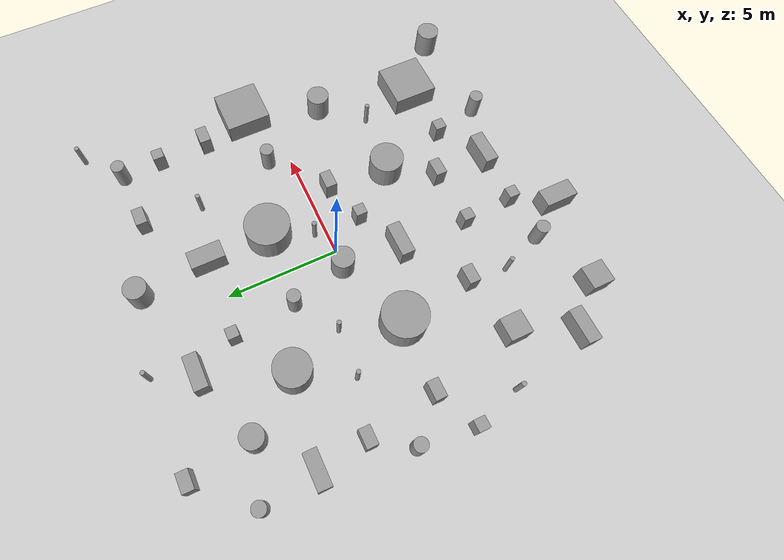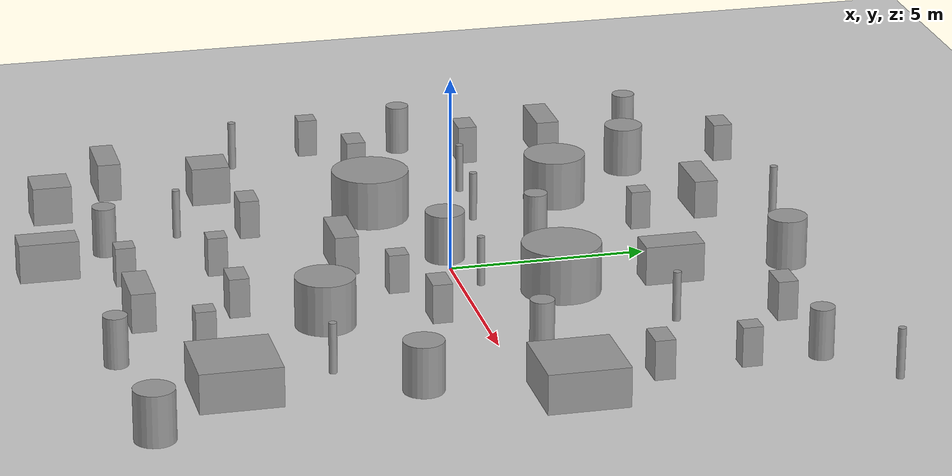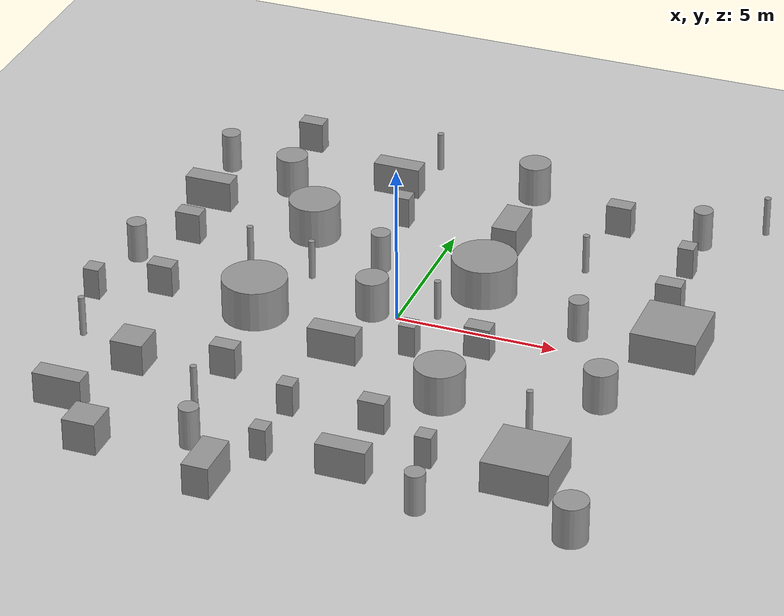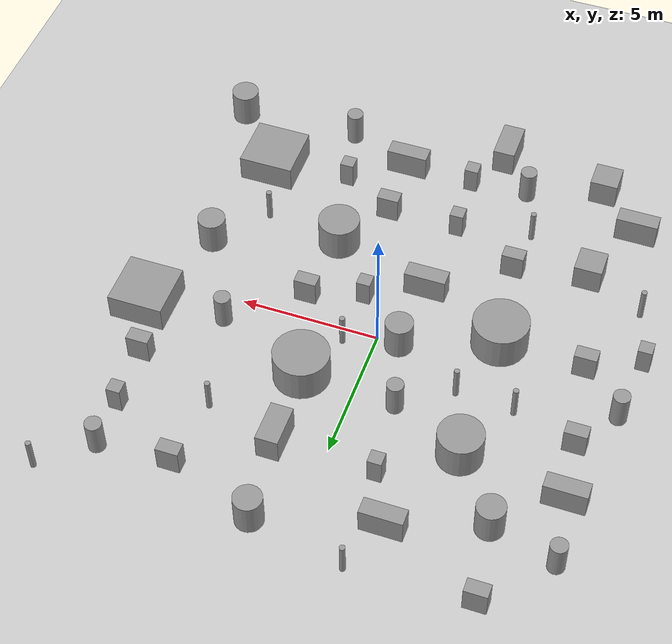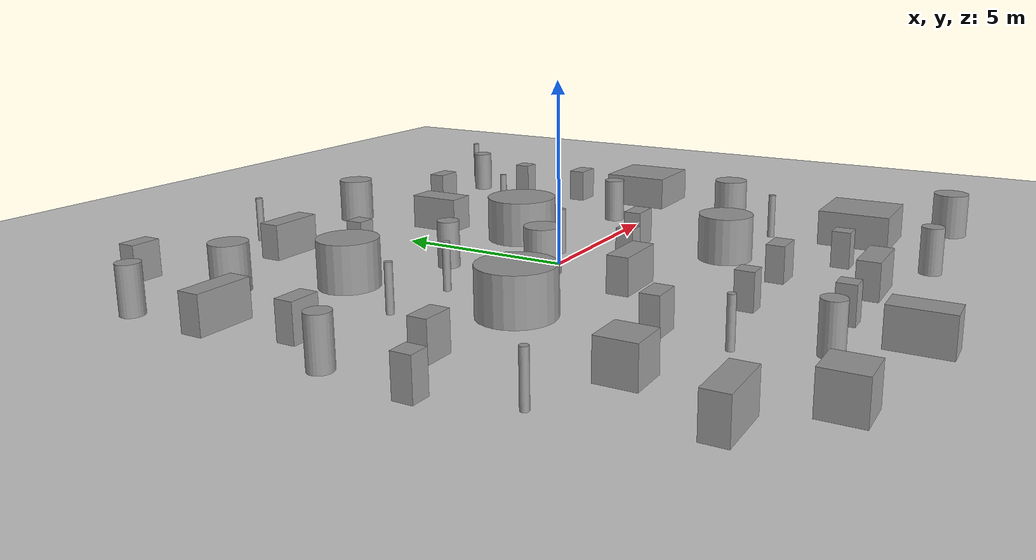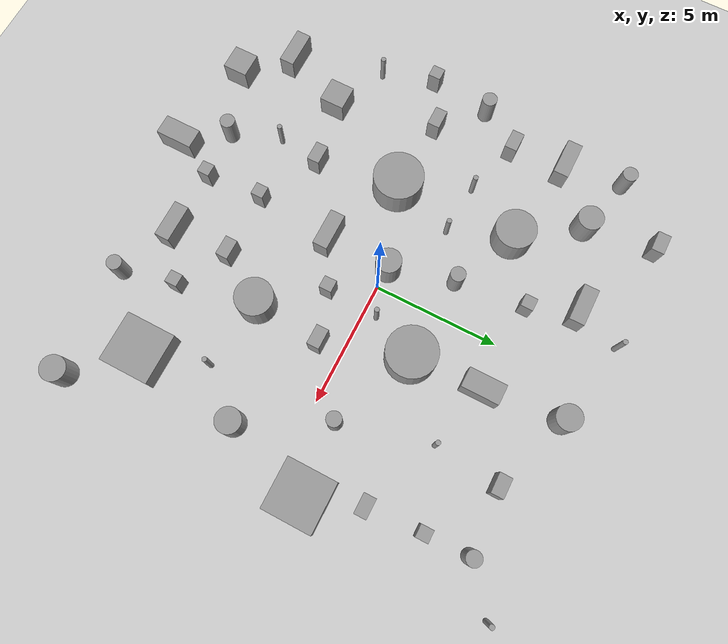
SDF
<sdf version="1.7">
 <world name="default">
  <light name="sun" type="directional">
   <pose>0 0 10 0 -0 0</pose>
   <diffuse>0.8 0.8 0.8 1</diffuse>
   <specular>0.2 0.2 0.2 1</specular>
   <attenuation>
    <range>1000</range>
    <constant>0.9</constant>
    <linear>0.01</linear>
    <quadratic>0.001</quadratic>
   </attenuation>
   <direction>-0.5 0.1 -0.9</direction>
   <spot><inner_angle>0</inner_angle><outer_angle>0</outer_angle><falloff>0</falloff></spot>
  </light>
  <model name="ground_plane">
   <static>1</static>
   <link name="link">
    <collision name="collision">
     <geometry><plane><normal>0 0 1</normal><size>100 100</size></plane></geometry>
     <surface>
      <contact><collide_bitmask>65535</collide_bitmask></contact>
      <friction><ode><mu>100</mu><mu2>50</mu2></ode></friction>
     </surface>
    </collision>
    <visual name="visual">
     <cast_shadows>0</cast_shadows>
     <geometry><plane><normal>0 0 1</normal><size>100 100</size></plane></geometry>
     <material>
      <script><uri>file://media/materials/scripts/gazebo.material</uri><name>Gazebo/Grey</name></script>
     </material>
    </visual>
   </link>
  </model>
  <gravity>0 0 -9.8</gravity>
  <magnetic_field>6e-06 2.3e-05 -4.2e-05</magnetic_field>
  <atmosphere type="adiabatic"/>
  <physics type="ode">
   <max_step_size>0.001</max_step_size>
   <real_time_factor>1</real_time_factor>
   <real_time_update_rate>500</real_time_update_rate>
  </physics>
  <scene><ambient>0.4 0.4 0.4 1</ambient><background>0.7 0.7 0.7 1</background><shadows>1</shadows></scene>
  <spherical_coordinates>
   <surface_model>EARTH_WGS84</surface_model>
   <latitude_deg>0</latitude_deg>
   <longitude_deg>0</longitude_deg>
   <elevation>0</elevation>
   <heading_deg>0</heading_deg>
  </spherical_coordinates>
  <model name="Untitled">
   <link name="link_0_clone_2">
    <inertial>
     <mass>1</mass>
     <inertia><ixx>0.145833</ixx><ixy>0</ixy><ixz>0</ixz><iyy>0.145833</iyy><iyz>0</iyz><izz>0.125</izz></inertia>
    </inertial>
    <pose>-3.58175 -0.821421 0 0 -0 0</pose>
    <visual name="visual">
     <geometry><cylinder><radius>1</radius><length>1.5</length></cylinder></geometry>
     <material>
      <lighting>1</lighting>
      <script><uri>file://media/materials/scripts/gazebo.material</uri><name>Gazebo/Grey</name></script>
      <shader type="pixel"><normal_map>__default__</normal_map></shader>
      <ambient>0.3 0.3 0.3 1</ambient>
      <diffuse>0.7 0.7 0.7 1</diffuse>
      <specular>0.01 0.01 0.01 1</specular>
      <emissive>0 0 0 1</emissive>
     </material>
    </visual>
    <collision name="collision">
     <geometry><cylinder><radius>1</radius><length>1.5</length></cylinder></geometry>
     <surface>
      <friction>
       <ode><mu>1</mu><mu2>1</mu2><fdir1>0 0 0</fdir1><slip1>0</slip1><slip2>0</slip2></ode>
       <torsional>
        <coefficient>1</coefficient>
        <patch_radius>0</patch_radius>
        <surface_radius>0</surface_radius>
        <use_patch_radius>1</use_patch_radius>
        <ode><slip>0</slip></ode>
       </torsional>
      </friction>
      <bounce><restitution_coefficient>0</restitution_coefficient><threshold>1e+06</threshold></bounce>
      <contact>
       <collide_without_contact>0</collide_without_contact>
       <collide_without_contact_bitmask>1</collide_without_contact_bitmask>
       <collide_bitmask>1</collide_bitmask>
       <ode>
        <soft_cfm>0</soft_cfm>
        <soft_erp>0.2</soft_erp>
        <kp>1e+13</kp>
        <kd>1</kd>
        <max_vel>0.01</max_vel>
        <min_depth>0</min_depth>
       </ode>
       <bullet>
        <split_impulse>1</split_impulse>
        <split_impulse_penetration_threshold>-0.01</split_impulse_penetration_threshold>
        <soft_cfm>0</soft_cfm>
        <soft_erp>0.2</soft_erp>
        <kp>1e+13</kp>
        <kd>1</kd>
       </bullet>
      </contact>
     </surface>
    </collision>
   </link>
   <link name="link_0_clone_2_clone">
    <inertial>
     <mass>1</mass>
     <inertia><ixx>0.145833</ixx><ixy>0</ixy><ixz>0</ixz><iyy>0.145833</iyy><iyz>0</iyz><izz>0.125</izz></inertia>
    </inertial>
    <pose>4.8968 4.95603 0 0 -0 0</pose>
    <visual name="visual">
     <geometry><cylinder><radius>0.1</radius><length>1.5</length></cylinder></geometry>
     <material>
      <lighting>1</lighting>
      <script><uri>file://media/materials/scripts/gazebo.material</uri><name>Gazebo/Grey</name></script>
      <shader type="pixel"><normal_map>__default__</normal_map></shader>
      <ambient>0.3 0.3 0.3 1</ambient>
      <diffuse>0.7 0.7 0.7 1</diffuse>
      <specular>0.01 0.01 0.01 1</specular>
      <emissive>0 0 0 1</emissive>
     </material>
    </visual>
    <collision name="collision">
     <geometry><cylinder><radius>0.1</radius><length>1.5</length></cylinder></geometry>
     <surface>
      <friction>
       <ode><mu>1</mu><mu2>1</mu2><fdir1>0 0 0</fdir1><slip1>0</slip1><slip2>0</slip2></ode>
       <torsional>
        <coefficient>1</coefficient>
        <patch_radius>0</patch_radius>
        <surface_radius>0</surface_radius>
        <use_patch_radius>1</use_patch_radius>
        <ode><slip>0</slip></ode>
       </torsional>
      </friction>
      <bounce><restitution_coefficient>0</restitution_coefficient><threshold>1e+06</threshold></bounce>
      <contact>
       <collide_without_contact>0</collide_without_contact>
       <collide_without_contact_bitmask>1</collide_without_contact_bitmask>
       <collide_bitmask>1</collide_bitmask>
       <ode>
        <soft_cfm>0</soft_cfm>
        <soft_erp>0.2</soft_erp>
        <kp>1e+13</kp>
        <kd>1</kd>
        <max_vel>0.01</max_vel>
        <min_depth>0</min_depth>
       </ode>
       <bullet>
        <split_impulse>1</split_impulse>
        <split_impulse_penetration_threshold>-0.01</split_impulse_penetration_threshold>
        <soft_cfm>0</soft_cfm>
        <soft_erp>0.2</soft_erp>
        <kp>1e+13</kp>
        <kd>1</kd>
       </bullet>
      </contact>
     </surface>
    </collision>
   </link>
   <link name="link_0_clone_2_clone_0">
    <inertial>
     <mass>1</mass>
     <inertia><ixx>0.145833</ixx><ixy>0</ixy><ixz>0</ixz><iyy>0.145833</iyy><iyz>0</iyz><izz>0.125</izz></inertia>
    </inertial>
    <pose>3.23735 -3.40168 0 0 -0 0</pose>
    <visual name="visual">
     <geometry><cylinder><radius>0.75</radius><length>1.5</length></cylinder></geometry>
     <material>
      <lighting>1</lighting>
      <script><uri>file://media/materials/scripts/gazebo.material</uri><name>Gazebo/Grey</name></script>
      <shader type="pixel"><normal_map>__default__</normal_map></shader>
      <ambient>0.3 0.3 0.3 1</ambient>
      <diffuse>0.7 0.7 0.7 1</diffuse>
      <specular>0.01 0.01 0.01 1</specular>
      <emissive>0 0 0 1</emissive>
     </material>
    </visual>
    <collision name="collision">
     <geometry><cylinder><radius>0.75</radius><length>1.5</length></cylinder></geometry>
     <surface>
      <friction>
       <ode><mu>1</mu><mu2>1</mu2><fdir1>0 0 0</fdir1><slip1>0</slip1><slip2>0</slip2></ode>
       <torsional>
        <coefficient>1</coefficient>
        <patch_radius>0</patch_radius>
        <surface_radius>0</surface_radius>
        <use_patch_radius>1</use_patch_radius>
        <ode><slip>0</slip></ode>
       </torsional>
      </friction>
      <bounce><restitution_coefficient>0</restitution_coefficient><threshold>1e+06</threshold></bounce>
      <contact>
       <collide_without_contact>0</collide_without_contact>
       <collide_without_contact_bitmask>1</collide_without_contact_bitmask>
       <collide_bitmask>1</collide_bitmask>
       <ode>
        <soft_cfm>0</soft_cfm>
        <soft_erp>0.2</soft_erp>
        <kp>1e+13</kp>
        <kd>1</kd>
        <max_vel>0.01</max_vel>
        <min_depth>0</min_depth>
       </ode>
       <bullet>
        <split_impulse>1</split_impulse>
        <split_impulse_penetration_threshold>-0.01</split_impulse_penetration_threshold>
        <soft_cfm>0</soft_cfm>
        <soft_erp>0.2</soft_erp>
        <kp>1e+13</kp>
        <kd>1</kd>
       </bullet>
      </contact>
     </surface>
    </collision>
   </link>
   <link name="link_0_clone_2_clone_0_clone">
    <inertial>
     <mass>1</mass>
     <inertia><ixx>0.145833</ixx><ixy>0</ixy><ixz>0</ixz><iyy>0.145833</iyy><iyz>0</iyz><izz>0.125</izz></inertia>
    </inertial>
    <pose>5.84252 1.33545 0 0 -0 0</pose>
    <visual name="visual">
     <geometry><cylinder><radius>0.3</radius><length>1.5</length></cylinder></geometry>
     <material>
      <lighting>1</lighting>
      <script><uri>file://media/materials/scripts/gazebo.material</uri><name>Gazebo/Grey</name></script>
      <shader type="pixel"><normal_map>__default__</normal_map></shader>
      <ambient>0.3 0.3 0.3 1</ambient>
      <diffuse>0.7 0.7 0.7 1</diffuse>
      <specular>0.01 0.01 0.01 1</specular>
      <emissive>0 0 0 1</emissive>
     </material>
    </visual>
    <collision name="collision">
     <geometry><cylinder><radius>0.3</radius><length>1.5</length></cylinder></geometry>
     <surface>
      <friction>
       <ode><mu>1</mu><mu2>1</mu2><fdir1>0 0 0</fdir1><slip1>0</slip1><slip2>0</slip2></ode>
       <torsional>
        <coefficient>1</coefficient>
        <patch_radius>0</patch_radius>
        <surface_radius>0</surface_radius>
        <use_patch_radius>1</use_patch_radius>
        <ode><slip>0</slip></ode>
       </torsional>
      </friction>
      <bounce><restitution_coefficient>0</restitution_coefficient><threshold>1e+06</threshold></bounce>
      <contact>
       <collide_without_contact>0</collide_without_contact>
       <collide_without_contact_bitmask>1</collide_without_contact_bitmask>
       <collide_bitmask>1</collide_bitmask>
       <ode>
        <soft_cfm>0</soft_cfm>
        <soft_erp>0.2</soft_erp>
        <kp>1e+13</kp>
        <kd>1</kd>
        <max_vel>0.01</max_vel>
        <min_depth>0</min_depth>
       </ode>
       <bullet>
        <split_impulse>1</split_impulse>
        <split_impulse_penetration_threshold>-0.01</split_impulse_penetration_threshold>
        <soft_cfm>0</soft_cfm>
        <soft_erp>0.2</soft_erp>
        <kp>1e+13</kp>
        <kd>1</kd>
       </bullet>
      </contact>
     </surface>
    </collision>
   </link>
   <link name="link_0_clone_2_clone_0_clone_clone">
    <inertial>
     <mass>1</mass>
     <inertia><ixx>0.145833</ixx><ixy>0</ixy><ixz>0</ixz><iyy>0.145833</iyy><iyz>0</iyz><izz>0.125</izz></inertia>
    </inertial>
    <pose>7.78458 7.68648 0 0 -0 0</pose>
    <visual name="visual">
     <geometry><cylinder><radius>0.3</radius><length>1.5</length></cylinder></geometry>
     <material>
      <lighting>1</lighting>
      <script><uri>file://media/materials/scripts/gazebo.material</uri><name>Gazebo/Grey</name></script>
      <shader type="pixel"><normal_map>__default__</normal_map></shader>
      <ambient>0.3 0.3 0.3 1</ambient>
      <diffuse>0.7 0.7 0.7 1</diffuse>
      <specular>0.01 0.01 0.01 1</specular>
      <emissive>0 0 0 1</emissive>
     </material>
    </visual>
    <collision name="collision">
     <geometry><cylinder><radius>0.3</radius><length>1.5</length></cylinder></geometry>
     <surface>
      <friction>
       <ode><mu>1</mu><mu2>1</mu2><fdir1>0 0 0</fdir1><slip1>0</slip1><slip2>0</slip2></ode>
       <torsional>
        <coefficient>1</coefficient>
        <patch_radius>0</patch_radius>
        <surface_radius>0</surface_radius>
        <use_patch_radius>1</use_patch_radius>
        <ode><slip>0</slip></ode>
       </torsional>
      </friction>
      <bounce><restitution_coefficient>0</restitution_coefficient><threshold>1e+06</threshold></bounce>
      <contact>
       <collide_without_contact>0</collide_without_contact>
       <collide_without_contact_bitmask>1</collide_without_contact_bitmask>
       <collide_bitmask>1</collide_bitmask>
       <ode>
        <soft_cfm>0</soft_cfm>
        <soft_erp>0.2</soft_erp>
        <kp>1e+13</kp>
        <kd>1</kd>
        <max_vel>0.01</max_vel>
        <min_depth>0</min_depth>
       </ode>
       <bullet>
        <split_impulse>1</split_impulse>
        <split_impulse_penetration_threshold>-0.01</split_impulse_penetration_threshold>
        <soft_cfm>0</soft_cfm>
        <soft_erp>0.2</soft_erp>
        <kp>1e+13</kp>
        <kd>1</kd>
       </bullet>
      </contact>
     </surface>
    </collision>
   </link>
   <link name="link_0_clone_2_clone_0_clone_clone_0">
    <inertial>
     <mass>1</mass>
     <inertia><ixx>0.145833</ixx><ixy>0</ixy><ixz>0</ixz><iyy>0.145833</iyy><iyz>0</iyz><izz>0.125</izz></inertia>
    </inertial>
    <pose>-2.57481 -7.91493 0 0 -0 0</pose>
    <visual name="visual">
     <geometry><cylinder><radius>0.3</radius><length>1.5</length></cylinder></geometry>
     <material>
      <lighting>1</lighting>
      <script><uri>file://media/materials/scripts/gazebo.material</uri><name>Gazebo/Grey</name></script>
      <shader type="pixel"><normal_map>__default__</normal_map></shader>
      <ambient>0.3 0.3 0.3 1</ambient>
      <diffuse>0.7 0.7 0.7 1</diffuse>
      <specular>0.01 0.01 0.01 1</specular>
      <emissive>0 0 0 1</emissive>
     </material>
    </visual>
    <collision name="collision">
     <geometry><cylinder><radius>0.3</radius><length>1.5</length></cylinder></geometry>
     <surface>
      <friction>
       <ode><mu>1</mu><mu2>1</mu2><fdir1>0 0 0</fdir1><slip1>0</slip1><slip2>0</slip2></ode>
       <torsional>
        <coefficient>1</coefficient>
        <patch_radius>0</patch_radius>
        <surface_radius>0</surface_radius>
        <use_patch_radius>1</use_patch_radius>
        <ode><slip>0</slip></ode>
       </torsional>
      </friction>
      <bounce><restitution_coefficient>0</restitution_coefficient><threshold>1e+06</threshold></bounce>
      <contact>
       <collide_without_contact>0</collide_without_contact>
       <collide_without_contact_bitmask>1</collide_without_contact_bitmask>
       <collide_bitmask>1</collide_bitmask>
       <ode>
        <soft_cfm>0</soft_cfm>
        <soft_erp>0.2</soft_erp>
        <kp>1e+13</kp>
        <kd>1</kd>
        <max_vel>0.01</max_vel>
        <min_depth>0</min_depth>
       </ode>
       <bullet>
        <split_impulse>1</split_impulse>
        <split_impulse_penetration_threshold>-0.01</split_impulse_penetration_threshold>
        <soft_cfm>0</soft_cfm>
        <soft_erp>0.2</soft_erp>
        <kp>1e+13</kp>
        <kd>1</kd>
       </bullet>
      </contact>
     </surface>
    </collision>
   </link>
   <link name="link_0_clone_2_clone_0_clone_clone_1">
    <inertial>
     <mass>1</mass>
     <inertia><ixx>0.145833</ixx><ixy>0</ixy><ixz>0</ixz><iyy>0.145833</iyy><iyz>0</iyz><izz>0.125</izz></inertia>
    </inertial>
    <pose>-7.75767 7.14289 0 0 -0 0</pose>
    <visual name="visual">
     <geometry><cylinder><radius>0.3</radius><length>1.5</length></cylinder></geometry>
     <material>
      <lighting>1</lighting>
      <script><uri>file://media/materials/scripts/gazebo.material</uri><name>Gazebo/Grey</name></script>
      <shader type="pixel"><normal_map>__default__</normal_map></shader>
      <ambient>0.3 0.3 0.3 1</ambient>
      <diffuse>0.7 0.7 0.7 1</diffuse>
      <specular>0.01 0.01 0.01 1</specular>
      <emissive>0 0 0 1</emissive>
     </material>
    </visual>
    <collision name="collision">
     <geometry><cylinder><radius>0.3</radius><length>1.5</length></cylinder></geometry>
     <surface>
      <friction>
       <ode><mu>1</mu><mu2>1</mu2><fdir1>0 0 0</fdir1><slip1>0</slip1><slip2>0</slip2></ode>
       <torsional>
        <coefficient>1</coefficient>
        <patch_radius>0</patch_radius>
        <surface_radius>0</surface_radius>
        <use_patch_radius>1</use_patch_radius>
        <ode><slip>0</slip></ode>
       </torsional>
      </friction>
      <bounce><restitution_coefficient>0</restitution_coefficient><threshold>1e+06</threshold></bounce>
      <contact>
       <collide_without_contact>0</collide_without_contact>
       <collide_without_contact_bitmask>1</collide_without_contact_bitmask>
       <collide_bitmask>1</collide_bitmask>
       <ode>
        <soft_cfm>0</soft_cfm>
        <soft_erp>0.2</soft_erp>
        <kp>1e+13</kp>
        <kd>1</kd>
        <max_vel>0.01</max_vel>
        <min_depth>0</min_depth>
       </ode>
       <bullet>
        <split_impulse>1</split_impulse>
        <split_impulse_penetration_threshold>-0.01</split_impulse_penetration_threshold>
        <soft_cfm>0</soft_cfm>
        <soft_erp>0.2</soft_erp>
        <kp>1e+13</kp>
        <kd>1</kd>
       </bullet>
      </contact>
     </surface>
    </collision>
   </link>
   <link name="link_0_clone_2_clone_0_clone_clone_2">
    <inertial>
     <mass>1</mass>
     <inertia><ixx>0.145833</ixx><ixy>0</ixy><ixz>0</ixz><iyy>0.145833</iyy><iyz>0</iyz><izz>0.125</izz></inertia>
    </inertial>
    <pose>-1.01347 2.94075 0 0 -0 0</pose>
    <visual name="visual">
     <geometry><cylinder><radius>0.3</radius><length>1.5</length></cylinder></geometry>
     <material>
      <lighting>1</lighting>
      <script><uri>file://media/materials/scripts/gazebo.material</uri><name>Gazebo/Grey</name></script>
      <shader type="pixel"><normal_map>__default__</normal_map></shader>
      <ambient>0.3 0.3 0.3 1</ambient>
      <diffuse>0.7 0.7 0.7 1</diffuse>
      <specular>0.01 0.01 0.01 1</specular>
      <emissive>0 0 0 1</emissive>
     </material>
    </visual>
    <collision name="collision">
     <geometry><cylinder><radius>0.3</radius><length>1.5</length></cylinder></geometry>
     <surface>
      <friction>
       <ode><mu>1</mu><mu2>1</mu2><fdir1>0 0 0</fdir1><slip1>0</slip1><slip2>0</slip2></ode>
       <torsional>
        <coefficient>1</coefficient>
        <patch_radius>0</patch_radius>
        <surface_radius>0</surface_radius>
        <use_patch_radius>1</use_patch_radius>
        <ode><slip>0</slip></ode>
       </torsional>
      </friction>
      <bounce><restitution_coefficient>0</restitution_coefficient><threshold>1e+06</threshold></bounce>
      <contact>
       <collide_without_contact>0</collide_without_contact>
       <collide_without_contact_bitmask>1</collide_without_contact_bitmask>
       <collide_bitmask>1</collide_bitmask>
       <ode>
        <soft_cfm>0</soft_cfm>
        <soft_erp>0.2</soft_erp>
        <kp>1e+13</kp>
        <kd>1</kd>
        <max_vel>0.01</max_vel>
        <min_depth>0</min_depth>
       </ode>
       <bullet>
        <split_impulse>1</split_impulse>
        <split_impulse_penetration_threshold>-0.01</split_impulse_penetration_threshold>
        <soft_cfm>0</soft_cfm>
        <soft_erp>0.2</soft_erp>
        <kp>1e+13</kp>
        <kd>1</kd>
       </bullet>
      </contact>
     </surface>
    </collision>
   </link>
   <link name="link_0_clone_2_clone_0_clone_clone_3">
    <inertial>
     <mass>1</mass>
     <inertia><ixx>0.145833</ixx><ixy>0</ixy><ixz>0</ixz><iyy>0.145833</iyy><iyz>0</iyz><izz>0.125</izz></inertia>
    </inertial>
    <pose>4.47822 -8.70392 0 0 -0 0</pose>
    <visual name="visual">
     <geometry><cylinder><radius>0.3</radius><length>1.5</length></cylinder></geometry>
     <material>
      <lighting>1</lighting>
      <script><uri>file://media/materials/scripts/gazebo.material</uri><name>Gazebo/Grey</name></script>
      <shader type="pixel"><normal_map>__default__</normal_map></shader>
      <ambient>0.3 0.3 0.3 1</ambient>
      <diffuse>0.7 0.7 0.7 1</diffuse>
      <specular>0.01 0.01 0.01 1</specular>
      <emissive>0 0 0 1</emissive>
     </material>
    </visual>
    <collision name="collision">
     <geometry><cylinder><radius>0.3</radius><length>1.5</length></cylinder></geometry>
     <surface>
      <friction>
       <ode><mu>1</mu><mu2>1</mu2><fdir1>0 0 0</fdir1><slip1>0</slip1><slip2>0</slip2></ode>
       <torsional>
        <coefficient>1</coefficient>
        <patch_radius>0</patch_radius>
        <surface_radius>0</surface_radius>
        <use_patch_radius>1</use_patch_radius>
        <ode><slip>0</slip></ode>
       </torsional>
      </friction>
      <bounce><restitution_coefficient>0</restitution_coefficient><threshold>1e+06</threshold></bounce>
      <contact>
       <collide_without_contact>0</collide_without_contact>
       <collide_without_contact_bitmask>1</collide_without_contact_bitmask>
       <collide_bitmask>1</collide_bitmask>
       <ode>
        <soft_cfm>0</soft_cfm>
        <soft_erp>0.2</soft_erp>
        <kp>1e+13</kp>
        <kd>1</kd>
        <max_vel>0.01</max_vel>
        <min_depth>0</min_depth>
       </ode>
       <bullet>
        <split_impulse>1</split_impulse>
        <split_impulse_penetration_threshold>-0.01</split_impulse_penetration_threshold>
        <soft_cfm>0</soft_cfm>
        <soft_erp>0.2</soft_erp>
        <kp>1e+13</kp>
        <kd>1</kd>
       </bullet>
      </contact>
     </surface>
    </collision>
   </link>
   <link name="link_0_clone_2_clone_0_clone_clone_clone">
    <inertial>
     <mass>1</mass>
     <inertia><ixx>0.145833</ixx><ixy>0</ixy><ixz>0</ixz><iyy>0.145833</iyy><iyz>0</iyz><izz>0.125</izz></inertia>
    </inertial>
    <pose>-8.2311 0.933708 0 0 -0 0</pose>
    <visual name="visual">
     <geometry><cylinder><radius>0.3</radius><length>1.5</length></cylinder></geometry>
     <material>
      <lighting>1</lighting>
      <script><uri>file://media/materials/scripts/gazebo.material</uri><name>Gazebo/Grey</name></script>
      <shader type="pixel"><normal_map>__default__</normal_map></shader>
      <ambient>0.3 0.3 0.3 1</ambient>
      <diffuse>0.7 0.7 0.7 1</diffuse>
      <specular>0.01 0.01 0.01 1</specular>
      <emissive>0 0 0 1</emissive>
     </material>
    </visual>
    <collision name="collision">
     <geometry><cylinder><radius>0.3</radius><length>1.5</length></cylinder></geometry>
     <surface>
      <friction>
       <ode><mu>1</mu><mu2>1</mu2><fdir1>0 0 0</fdir1><slip1>0</slip1><slip2>0</slip2></ode>
       <torsional>
        <coefficient>1</coefficient>
        <patch_radius>0</patch_radius>
        <surface_radius>0</surface_radius>
        <use_patch_radius>1</use_patch_radius>
        <ode><slip>0</slip></ode>
       </torsional>
      </friction>
      <bounce><restitution_coefficient>0</restitution_coefficient><threshold>1e+06</threshold></bounce>
      <contact>
       <collide_without_contact>0</collide_without_contact>
       <collide_without_contact_bitmask>1</collide_without_contact_bitmask>
       <collide_bitmask>1</collide_bitmask>
       <ode>
        <soft_cfm>0</soft_cfm>
        <soft_erp>0.2</soft_erp>
        <kp>1e+13</kp>
        <kd>1</kd>
        <max_vel>0.01</max_vel>
        <min_depth>0</min_depth>
       </ode>
       <bullet>
        <split_impulse>1</split_impulse>
        <split_impulse_penetration_threshold>-0.01</split_impulse_penetration_threshold>
        <soft_cfm>0</soft_cfm>
        <soft_erp>0.2</soft_erp>
        <kp>1e+13</kp>
        <kd>1</kd>
       </bullet>
      </contact>
     </surface>
    </collision>
   </link>
   <link name="link_0_clone_2_clone_1">
    <inertial>
     <mass>1</mass>
     <inertia><ixx>0.145833</ixx><ixy>0</ixy><ixz>0</ixz><iyy>0.145833</iyy><iyz>0</iyz><izz>0.125</izz></inertia>
    </inertial>
    <pose>-3.66206 4.13062 0 0 -0 0</pose>
    <visual name="visual">
     <geometry><cylinder><radius>0.8</radius><length>1.5</length></cylinder></geometry>
     <material>
      <lighting>1</lighting>
      <script><uri>file://media/materials/scripts/gazebo.material</uri><name>Gazebo/Grey</name></script>
      <shader type="pixel"><normal_map>__default__</normal_map></shader>
      <ambient>0.3 0.3 0.3 1</ambient>
      <diffuse>0.7 0.7 0.7 1</diffuse>
      <specular>0.01 0.01 0.01 1</specular>
      <emissive>0 0 0 1</emissive>
     </material>
    </visual>
    <collision name="collision">
     <geometry><cylinder><radius>0.8</radius><length>1.5</length></cylinder></geometry>
     <surface>
      <friction>
       <ode><mu>1</mu><mu2>1</mu2><fdir1>0 0 0</fdir1><slip1>0</slip1><slip2>0</slip2></ode>
       <torsional>
        <coefficient>1</coefficient>
        <patch_radius>0</patch_radius>
        <surface_radius>0</surface_radius>
        <use_patch_radius>1</use_patch_radius>
        <ode><slip>0</slip></ode>
       </torsional>
      </friction>
      <bounce><restitution_coefficient>0</restitution_coefficient><threshold>1e+06</threshold></bounce>
      <contact>
       <collide_without_contact>0</collide_without_contact>
       <collide_without_contact_bitmask>1</collide_without_contact_bitmask>
       <collide_bitmask>1</collide_bitmask>
       <ode>
        <soft_cfm>0</soft_cfm>
        <soft_erp>0.2</soft_erp>
        <kp>1e+13</kp>
        <kd>1</kd>
        <max_vel>0.01</max_vel>
        <min_depth>0</min_depth>
       </ode>
       <bullet>
        <split_impulse>1</split_impulse>
        <split_impulse_penetration_threshold>-0.01</split_impulse_penetration_threshold>
        <soft_cfm>0</soft_cfm>
        <soft_erp>0.2</soft_erp>
        <kp>1e+13</kp>
        <kd>1</kd>
       </bullet>
      </contact>
     </surface>
    </collision>
   </link>
   <link name="link_0_clone_2_clone_2">
    <inertial>
     <mass>1</mass>
     <inertia><ixx>0.145833</ixx><ixy>0</ixy><ixz>0</ixz><iyy>0.145833</iyy><iyz>0</iyz><izz>0.125</izz></inertia>
    </inertial>
    <pose>2.40931 2.71499 0 0 -0 0</pose>
    <visual name="visual">
     <geometry><cylinder><radius>1</radius><length>1.5</length></cylinder></geometry>
     <material>
      <lighting>1</lighting>
      <script><uri>file://media/materials/scripts/gazebo.material</uri><name>Gazebo/Grey</name></script>
      <shader type="pixel"><normal_map>__default__</normal_map></shader>
      <ambient>0.3 0.3 0.3 1</ambient>
      <diffuse>0.7 0.7 0.7 1</diffuse>
      <specular>0.01 0.01 0.01 1</specular>
      <emissive>0 0 0 1</emissive>
     </material>
    </visual>
    <collision name="collision">
     <geometry><cylinder><radius>1</radius><length>1.5</length></cylinder></geometry>
     <surface>
      <friction>
       <ode><mu>1</mu><mu2>1</mu2><fdir1>0 0 0</fdir1><slip1>0</slip1><slip2>0</slip2></ode>
       <torsional>
        <coefficient>1</coefficient>
        <patch_radius>0</patch_radius>
        <surface_radius>0</surface_radius>
        <use_patch_radius>1</use_patch_radius>
        <ode><slip>0</slip></ode>
       </torsional>
      </friction>
      <bounce><restitution_coefficient>0</restitution_coefficient><threshold>1e+06</threshold></bounce>
      <contact>
       <collide_without_contact>0</collide_without_contact>
       <collide_without_contact_bitmask>1</collide_without_contact_bitmask>
       <collide_bitmask>1</collide_bitmask>
       <ode>
        <soft_cfm>0</soft_cfm>
        <soft_erp>0.2</soft_erp>
        <kp>1e+13</kp>
        <kd>1</kd>
        <max_vel>0.01</max_vel>
        <min_depth>0</min_depth>
       </ode>
       <bullet>
        <split_impulse>1</split_impulse>
        <split_impulse_penetration_threshold>-0.01</split_impulse_penetration_threshold>
        <soft_cfm>0</soft_cfm>
        <soft_erp>0.2</soft_erp>
        <kp>1e+13</kp>
        <kd>1</kd>
       </bullet>
      </contact>
     </surface>
    </collision>
   </link>
   <link name="link_0_clone_2_clone_clone">
    <inertial>
     <mass>1</mass>
     <inertia><ixx>0.145833</ixx><ixy>0</ixy><ixz>0</ixz><iyy>0.145833</iyy><iyz>0</iyz><izz>0.125</izz></inertia>
    </inertial>
    <pose>-5.37987 6.48036 0 0 -0 0</pose>
    <visual name="visual">
     <geometry><cylinder><radius>0.5</radius><length>1.5</length></cylinder></geometry>
     <material>
      <lighting>1</lighting>
      <script><uri>file://media/materials/scripts/gazebo.material</uri><name>Gazebo/Grey</name></script>
      <shader type="pixel"><normal_map>__default__</normal_map></shader>
      <ambient>0.3 0.3 0.3 1</ambient>
      <diffuse>0.7 0.7 0.7 1</diffuse>
      <specular>0.01 0.01 0.01 1</specular>
      <emissive>0 0 0 1</emissive>
     </material>
    </visual>
    <collision name="collision">
     <geometry><cylinder><radius>0.5</radius><length>1.5</length></cylinder></geometry>
     <surface>
      <friction>
       <ode><mu>1</mu><mu2>1</mu2><fdir1>0 0 0</fdir1><slip1>0</slip1><slip2>0</slip2></ode>
       <torsional>
        <coefficient>1</coefficient>
        <patch_radius>0</patch_radius>
        <surface_radius>0</surface_radius>
        <use_patch_radius>1</use_patch_radius>
        <ode><slip>0</slip></ode>
       </torsional>
      </friction>
      <bounce><restitution_coefficient>0</restitution_coefficient><threshold>1e+06</threshold></bounce>
      <contact>
       <collide_without_contact>0</collide_without_contact>
       <collide_without_contact_bitmask>1</collide_without_contact_bitmask>
       <collide_bitmask>1</collide_bitmask>
       <ode>
        <soft_cfm>0</soft_cfm>
        <soft_erp>0.2</soft_erp>
        <kp>1e+13</kp>
        <kd>1</kd>
        <max_vel>0.01</max_vel>
        <min_depth>0</min_depth>
       </ode>
       <bullet>
        <split_impulse>1</split_impulse>
        <split_impulse_penetration_threshold>-0.01</split_impulse_penetration_threshold>
        <soft_cfm>0</soft_cfm>
        <soft_erp>0.2</soft_erp>
        <kp>1e+13</kp>
        <kd>1</kd>
       </bullet>
      </contact>
     </surface>
    </collision>
   </link>
   <link name="link_0_clone_2_clone_clone_0">
    <inertial>
     <mass>1</mass>
     <inertia><ixx>0.145833</ixx><ixy>0</ixy><ixz>0</ixz><iyy>0.145833</iyy><iyz>0</iyz><izz>0.125</izz></inertia>
    </inertial>
    <pose>-4.86844 1.87102 0 0 -0 0</pose>
    <visual name="visual">
     <geometry><cylinder><radius>0.1</radius><length>1.5</length></cylinder></geometry>
     <material>
      <lighting>1</lighting>
      <script><uri>file://media/materials/scripts/gazebo.material</uri><name>Gazebo/Grey</name></script>
      <shader type="pixel"><normal_map>__default__</normal_map></shader>
      <ambient>0.3 0.3 0.3 1</ambient>
      <diffuse>0.7 0.7 0.7 1</diffuse>
      <specular>0.01 0.01 0.01 1</specular>
      <emissive>0 0 0 1</emissive>
     </material>
    </visual>
    <collision name="collision">
     <geometry><cylinder><radius>0.1</radius><length>1.5</length></cylinder></geometry>
     <surface>
      <friction>
       <ode><mu>1</mu><mu2>1</mu2><fdir1>0 0 0</fdir1><slip1>0</slip1><slip2>0</slip2></ode>
       <torsional>
        <coefficient>1</coefficient>
        <patch_radius>0</patch_radius>
        <surface_radius>0</surface_radius>
        <use_patch_radius>1</use_patch_radius>
        <ode><slip>0</slip></ode>
       </torsional>
      </friction>
      <bounce><restitution_coefficient>0</restitution_coefficient><threshold>1e+06</threshold></bounce>
      <contact>
       <collide_without_contact>0</collide_without_contact>
       <collide_without_contact_bitmask>1</collide_without_contact_bitmask>
       <collide_bitmask>1</collide_bitmask>
       <ode>
        <soft_cfm>0</soft_cfm>
        <soft_erp>0.2</soft_erp>
        <kp>1e+13</kp>
        <kd>1</kd>
        <max_vel>0.01</max_vel>
        <min_depth>0</min_depth>
       </ode>
       <bullet>
        <split_impulse>1</split_impulse>
        <split_impulse_penetration_threshold>-0.01</split_impulse_penetration_threshold>
        <soft_cfm>0</soft_cfm>
        <soft_erp>0.2</soft_erp>
        <kp>1e+13</kp>
        <kd>1</kd>
       </bullet>
      </contact>
     </surface>
    </collision>
   </link>
   <link name="link_0_clone_2_clone_clone_1">
    <inertial>
     <mass>1</mass>
     <inertia><ixx>0.145833</ixx><ixy>0</ixy><ixz>0</ixz><iyy>0.145833</iyy><iyz>0</iyz><izz>0.125</izz></inertia>
    </inertial>
    <pose>-7.90099 -3.66902 0 0 -0 0</pose>
    <visual name="visual">
     <geometry><cylinder><radius>0.1</radius><length>1.5</length></cylinder></geometry>
     <material>
      <lighting>1</lighting>
      <script><uri>file://media/materials/scripts/gazebo.material</uri><name>Gazebo/Grey</name></script>
      <shader type="pixel"><normal_map>__default__</normal_map></shader>
      <ambient>0.3 0.3 0.3 1</ambient>
      <diffuse>0.7 0.7 0.7 1</diffuse>
      <specular>0.01 0.01 0.01 1</specular>
      <emissive>0 0 0 1</emissive>
     </material>
    </visual>
    <collision name="collision">
     <geometry><cylinder><radius>0.1</radius><length>1.5</length></cylinder></geometry>
     <surface>
      <friction>
       <ode><mu>1</mu><mu2>1</mu2><fdir1>0 0 0</fdir1><slip1>0</slip1><slip2>0</slip2></ode>
       <torsional>
        <coefficient>1</coefficient>
        <patch_radius>0</patch_radius>
        <surface_radius>0</surface_radius>
        <use_patch_radius>1</use_patch_radius>
        <ode><slip>0</slip></ode>
       </torsional>
      </friction>
      <bounce><restitution_coefficient>0</restitution_coefficient><threshold>1e+06</threshold></bounce>
      <contact>
       <collide_without_contact>0</collide_without_contact>
       <collide_without_contact_bitmask>1</collide_without_contact_bitmask>
       <collide_bitmask>1</collide_bitmask>
       <ode>
        <soft_cfm>0</soft_cfm>
        <soft_erp>0.2</soft_erp>
        <kp>1e+13</kp>
        <kd>1</kd>
        <max_vel>0.01</max_vel>
        <min_depth>0</min_depth>
       </ode>
       <bullet>
        <split_impulse>1</split_impulse>
        <split_impulse_penetration_threshold>-0.01</split_impulse_penetration_threshold>
        <soft_cfm>0</soft_cfm>
        <soft_erp>0.2</soft_erp>
        <kp>1e+13</kp>
        <kd>1</kd>
       </bullet>
      </contact>
     </surface>
    </collision>
   </link>
   <link name="link_0_clone_2_clone_clone_2">
    <inertial>
     <mass>1</mass>
     <inertia><ixx>0.145833</ixx><ixy>0</ixy><ixz>0</ixz><iyy>0.145833</iyy><iyz>0</iyz><izz>0.125</izz></inertia>
    </inertial>
    <pose>-3.29838 -5.94972 0 0 -0 0</pose>
    <visual name="visual">
     <geometry><cylinder><radius>0.1</radius><length>1.5</length></cylinder></geometry>
     <material>
      <lighting>1</lighting>
      <script><uri>file://media/materials/scripts/gazebo.material</uri><name>Gazebo/Grey</name></script>
      <shader type="pixel"><normal_map>__default__</normal_map></shader>
      <ambient>0.3 0.3 0.3 1</ambient>
      <diffuse>0.7 0.7 0.7 1</diffuse>
      <specular>0.01 0.01 0.01 1</specular>
      <emissive>0 0 0 1</emissive>
     </material>
    </visual>
    <collision name="collision">
     <geometry><cylinder><radius>0.1</radius><length>1.5</length></cylinder></geometry>
     <surface>
      <friction>
       <ode><mu>1</mu><mu2>1</mu2><fdir1>0 0 0</fdir1><slip1>0</slip1><slip2>0</slip2></ode>
       <torsional>
        <coefficient>1</coefficient>
        <patch_radius>0</patch_radius>
        <surface_radius>0</surface_radius>
        <use_patch_radius>1</use_patch_radius>
        <ode><slip>0</slip></ode>
       </torsional>
      </friction>
      <bounce><restitution_coefficient>0</restitution_coefficient><threshold>1e+06</threshold></bounce>
      <contact>
       <collide_without_contact>0</collide_without_contact>
       <collide_without_contact_bitmask>1</collide_without_contact_bitmask>
       <collide_bitmask>1</collide_bitmask>
       <ode>
        <soft_cfm>0</soft_cfm>
        <soft_erp>0.2</soft_erp>
        <kp>1e+13</kp>
        <kd>1</kd>
        <max_vel>0.01</max_vel>
        <min_depth>0</min_depth>
       </ode>
       <bullet>
        <split_impulse>1</split_impulse>
        <split_impulse_penetration_threshold>-0.01</split_impulse_penetration_threshold>
        <soft_cfm>0</soft_cfm>
        <soft_erp>0.2</soft_erp>
        <kp>1e+13</kp>
        <kd>1</kd>
       </bullet>
      </contact>
     </surface>
    </collision>
   </link>
   <link name="link_0_clone_2_clone_clone_3">
    <inertial>
     <mass>1</mass>
     <inertia><ixx>0.145833</ixx><ixy>0</ixy><ixz>0</ixz><iyy>0.145833</iyy><iyz>0</iyz><izz>0.125</izz></inertia>
    </inertial>
    <pose>6.09566 -3.8057 0 0 -0 0</pose>
    <visual name="visual">
     <geometry><cylinder><radius>0.1</radius><length>1.5</length></cylinder></geometry>
     <material>
      <lighting>1</lighting>
      <script><uri>file://media/materials/scripts/gazebo.material</uri><name>Gazebo/Grey</name></script>
      <shader type="pixel"><normal_map>__default__</normal_map></shader>
      <ambient>0.3 0.3 0.3 1</ambient>
      <diffuse>0.7 0.7 0.7 1</diffuse>
      <specular>0.01 0.01 0.01 1</specular>
      <emissive>0 0 0 1</emissive>
     </material>
    </visual>
    <collision name="collision">
     <geometry><cylinder><radius>0.1</radius><length>1.5</length></cylinder></geometry>
     <surface>
      <friction>
       <ode><mu>1</mu><mu2>1</mu2><fdir1>0 0 0</fdir1><slip1>0</slip1><slip2>0</slip2></ode>
       <torsional>
        <coefficient>1</coefficient>
        <patch_radius>0</patch_radius>
        <surface_radius>0</surface_radius>
        <use_patch_radius>1</use_patch_radius>
        <ode><slip>0</slip></ode>
       </torsional>
      </friction>
      <bounce><restitution_coefficient>0</restitution_coefficient><threshold>1e+06</threshold></bounce>
      <contact>
       <collide_without_contact>0</collide_without_contact>
       <collide_without_contact_bitmask>1</collide_without_contact_bitmask>
       <collide_bitmask>1</collide_bitmask>
       <ode>
        <soft_cfm>0</soft_cfm>
        <soft_erp>0.2</soft_erp>
        <kp>1e+13</kp>
        <kd>1</kd>
        <max_vel>0.01</max_vel>
        <min_depth>0</min_depth>
       </ode>
       <bullet>
        <split_impulse>1</split_impulse>
        <split_impulse_penetration_threshold>-0.01</split_impulse_penetration_threshold>
        <soft_cfm>0</soft_cfm>
        <soft_erp>0.2</soft_erp>
        <kp>1e+13</kp>
        <kd>1</kd>
       </bullet>
      </contact>
     </surface>
    </collision>
   </link>
   <link name="link_0_clone_2_clone_clone_4">
    <inertial>
     <mass>1</mass>
     <inertia><ixx>0.145833</ixx><ixy>0</ixy><ixz>0</ixz><iyy>0.145833</iyy><iyz>0</iyz><izz>0.125</izz></inertia>
    </inertial>
    <pose>-1.4611 9.43155 0 0 -0 0</pose>
    <visual name="visual">
     <geometry><cylinder><radius>0.1</radius><length>1.5</length></cylinder></geometry>
     <material>
      <lighting>1</lighting>
      <script><uri>file://media/materials/scripts/gazebo.material</uri><name>Gazebo/Grey</name></script>
      <shader type="pixel"><normal_map>__default__</normal_map></shader>
      <ambient>0.3 0.3 0.3 1</ambient>
      <diffuse>0.7 0.7 0.7 1</diffuse>
      <specular>0.01 0.01 0.01 1</specular>
      <emissive>0 0 0 1</emissive>
     </material>
    </visual>
    <collision name="collision">
     <geometry><cylinder><radius>0.1</radius><length>1.5</length></cylinder></geometry>
     <surface>
      <friction>
       <ode><mu>1</mu><mu2>1</mu2><fdir1>0 0 0</fdir1><slip1>0</slip1><slip2>0</slip2></ode>
       <torsional>
        <coefficient>1</coefficient>
        <patch_radius>0</patch_radius>
        <surface_radius>0</surface_radius>
        <use_patch_radius>1</use_patch_radius>
        <ode><slip>0</slip></ode>
       </torsional>
      </friction>
      <bounce><restitution_coefficient>0</restitution_coefficient><threshold>1e+06</threshold></bounce>
      <contact>
       <collide_without_contact>0</collide_without_contact>
       <collide_without_contact_bitmask>1</collide_without_contact_bitmask>
       <collide_bitmask>1</collide_bitmask>
       <ode>
        <soft_cfm>0</soft_cfm>
        <soft_erp>0.2</soft_erp>
        <kp>1e+13</kp>
        <kd>1</kd>
        <max_vel>0.01</max_vel>
        <min_depth>0</min_depth>
       </ode>
       <bullet>
        <split_impulse>1</split_impulse>
        <split_impulse_penetration_threshold>-0.01</split_impulse_penetration_threshold>
        <soft_cfm>0</soft_cfm>
        <soft_erp>0.2</soft_erp>
        <kp>1e+13</kp>
        <kd>1</kd>
       </bullet>
      </contact>
     </surface>
    </collision>
   </link>
   <link name="link_0_clone_2_clone_clone_5">
    <inertial>
     <mass>1</mass>
     <inertia><ixx>0.145833</ixx><ixy>0</ixy><ixz>0</ixz><iyy>0.145833</iyy><iyz>0</iyz><izz>0.125</izz></inertia>
    </inertial>
    <pose>9.43282 9.09032 0 0 -0 0</pose>
    <visual name="visual">
     <geometry><cylinder><radius>0.1</radius><length>1.5</length></cylinder></geometry>
     <material>
      <lighting>1</lighting>
      <script><uri>file://media/materials/scripts/gazebo.material</uri><name>Gazebo/Grey</name></script>
      <shader type="pixel"><normal_map>__default__</normal_map></shader>
      <ambient>0.3 0.3 0.3 1</ambient>
      <diffuse>0.7 0.7 0.7 1</diffuse>
      <specular>0.01 0.01 0.01 1</specular>
      <emissive>0 0 0 1</emissive>
     </material>
    </visual>
    <collision name="collision">
     <geometry><cylinder><radius>0.1</radius><length>1.5</length></cylinder></geometry>
     <surface>
      <friction>
       <ode><mu>1</mu><mu2>1</mu2><fdir1>0 0 0</fdir1><slip1>0</slip1><slip2>0</slip2></ode>
       <torsional>
        <coefficient>1</coefficient>
        <patch_radius>0</patch_radius>
        <surface_radius>0</surface_radius>
        <use_patch_radius>1</use_patch_radius>
        <ode><slip>0</slip></ode>
       </torsional>
      </friction>
      <bounce><restitution_coefficient>0</restitution_coefficient><threshold>1e+06</threshold></bounce>
      <contact>
       <collide_without_contact>0</collide_without_contact>
       <collide_without_contact_bitmask>1</collide_without_contact_bitmask>
       <collide_bitmask>1</collide_bitmask>
       <ode>
        <soft_cfm>0</soft_cfm>
        <soft_erp>0.2</soft_erp>
        <kp>1e+13</kp>
        <kd>1</kd>
        <max_vel>0.01</max_vel>
        <min_depth>0</min_depth>
       </ode>
       <bullet>
        <split_impulse>1</split_impulse>
        <split_impulse_penetration_threshold>-0.01</split_impulse_penetration_threshold>
        <soft_cfm>0</soft_cfm>
        <soft_erp>0.2</soft_erp>
        <kp>1e+13</kp>
        <kd>1</kd>
       </bullet>
      </contact>
     </surface>
    </collision>
   </link>
   <link name="link_0_clone_2_clone_clone_6">
    <inertial>
     <mass>1</mass>
     <inertia><ixx>0.145833</ixx><ixy>0</ixy><ixz>0</ixz><iyy>0.145833</iyy><iyz>0</iyz><izz>0.125</izz></inertia>
    </inertial>
    <pose>1.5952 0.872263 0 0 -0 0</pose>
    <visual name="visual">
     <geometry><cylinder><radius>0.1</radius><length>1.5</length></cylinder></geometry>
     <material>
      <lighting>1</lighting>
      <script><uri>file://media/materials/scripts/gazebo.material</uri><name>Gazebo/Grey</name></script>
      <shader type="pixel"><normal_map>__default__</normal_map></shader>
      <ambient>0.3 0.3 0.3 1</ambient>
      <diffuse>0.7 0.7 0.7 1</diffuse>
      <specular>0.01 0.01 0.01 1</specular>
      <emissive>0 0 0 1</emissive>
     </material>
    </visual>
    <collision name="collision">
     <geometry><cylinder><radius>0.1</radius><length>1.5</length></cylinder></geometry>
     <surface>
      <friction>
       <ode><mu>1</mu><mu2>1</mu2><fdir1>0 0 0</fdir1><slip1>0</slip1><slip2>0</slip2></ode>
       <torsional>
        <coefficient>1</coefficient>
        <patch_radius>0</patch_radius>
        <surface_radius>0</surface_radius>
        <use_patch_radius>1</use_patch_radius>
        <ode><slip>0</slip></ode>
       </torsional>
      </friction>
      <bounce><restitution_coefficient>0</restitution_coefficient><threshold>1e+06</threshold></bounce>
      <contact>
       <collide_without_contact>0</collide_without_contact>
       <collide_without_contact_bitmask>1</collide_without_contact_bitmask>
       <collide_bitmask>1</collide_bitmask>
       <ode>
        <soft_cfm>0</soft_cfm>
        <soft_erp>0.2</soft_erp>
        <kp>1e+13</kp>
        <kd>1</kd>
        <max_vel>0.01</max_vel>
        <min_depth>0</min_depth>
       </ode>
       <bullet>
        <split_impulse>1</split_impulse>
        <split_impulse_penetration_threshold>-0.01</split_impulse_penetration_threshold>
        <soft_cfm>0</soft_cfm>
        <soft_erp>0.2</soft_erp>
        <kp>1e+13</kp>
        <kd>1</kd>
       </bullet>
      </contact>
     </surface>
    </collision>
   </link>
   <link name="link_0_clone_2_clone_clone_6_clone">
    <inertial>
     <mass>1</mass>
     <inertia><ixx>0.145833</ixx><ixy>0</ixy><ixz>0</ixz><iyy>0.145833</iyy><iyz>0</iyz><izz>0.125</izz></inertia>
    </inertial>
    <pose>-2.78369 1.73127 0 0 -0 0</pose>
    <visual name="visual">
     <geometry><cylinder><radius>0.1</radius><length>1.5</length></cylinder></geometry>
     <material>
      <lighting>1</lighting>
      <script><uri>file://media/materials/scripts/gazebo.material</uri><name>Gazebo/Grey</name></script>
      <shader type="pixel"><normal_map>__default__</normal_map></shader>
      <ambient>0.3 0.3 0.3 1</ambient>
      <diffuse>0.7 0.7 0.7 1</diffuse>
      <specular>0.01 0.01 0.01 1</specular>
      <emissive>0 0 0 1</emissive>
     </material>
    </visual>
    <collision name="collision">
     <geometry><cylinder><radius>0.1</radius><length>1.5</length></cylinder></geometry>
     <surface>
      <friction>
       <ode><mu>1</mu><mu2>1</mu2><fdir1>0 0 0</fdir1><slip1>0</slip1><slip2>0</slip2></ode>
       <torsional>
        <coefficient>1</coefficient>
        <patch_radius>0</patch_radius>
        <surface_radius>0</surface_radius>
        <use_patch_radius>1</use_patch_radius>
        <ode><slip>0</slip></ode>
       </torsional>
      </friction>
      <bounce><restitution_coefficient>0</restitution_coefficient><threshold>1e+06</threshold></bounce>
      <contact>
       <collide_without_contact>0</collide_without_contact>
       <collide_without_contact_bitmask>1</collide_without_contact_bitmask>
       <collide_bitmask>1</collide_bitmask>
       <ode>
        <soft_cfm>0</soft_cfm>
        <soft_erp>0.2</soft_erp>
        <kp>1e+13</kp>
        <kd>1</kd>
        <max_vel>0.01</max_vel>
        <min_depth>0</min_depth>
       </ode>
       <bullet>
        <split_impulse>1</split_impulse>
        <split_impulse_penetration_threshold>-0.01</split_impulse_penetration_threshold>
        <soft_cfm>0</soft_cfm>
        <soft_erp>0.2</soft_erp>
        <kp>1e+13</kp>
        <kd>1</kd>
       </bullet>
      </contact>
     </surface>
    </collision>
   </link>
   <link name="link_0_clone_2_clone_clone_clone">
    <inertial>
     <mass>1</mass>
     <inertia><ixx>0.145833</ixx><ixy>0</ixy><ixz>0</ixz><iyy>0.145833</iyy><iyz>0</iyz><izz>0.125</izz></inertia>
    </inertial>
    <pose>7.59609 -1.95964 0 0 -0 0</pose>
    <visual name="visual">
     <geometry><cylinder><radius>0.5</radius><length>1.5</length></cylinder></geometry>
     <material>
      <lighting>1</lighting>
      <script><uri>file://media/materials/scripts/gazebo.material</uri><name>Gazebo/Grey</name></script>
      <shader type="pixel"><normal_map>__default__</normal_map></shader>
      <ambient>0.3 0.3 0.3 1</ambient>
      <diffuse>0.7 0.7 0.7 1</diffuse>
      <specular>0.01 0.01 0.01 1</specular>
      <emissive>0 0 0 1</emissive>
     </material>
    </visual>
    <collision name="collision">
     <geometry><cylinder><radius>0.5</radius><length>1.5</length></cylinder></geometry>
     <surface>
      <friction>
       <ode><mu>1</mu><mu2>1</mu2><fdir1>0 0 0</fdir1><slip1>0</slip1><slip2>0</slip2></ode>
       <torsional>
        <coefficient>1</coefficient>
        <patch_radius>0</patch_radius>
        <surface_radius>0</surface_radius>
        <use_patch_radius>1</use_patch_radius>
        <ode><slip>0</slip></ode>
       </torsional>
      </friction>
      <bounce><restitution_coefficient>0</restitution_coefficient><threshold>1e+06</threshold></bounce>
      <contact>
       <collide_without_contact>0</collide_without_contact>
       <collide_without_contact_bitmask>1</collide_without_contact_bitmask>
       <collide_bitmask>1</collide_bitmask>
       <ode>
        <soft_cfm>0</soft_cfm>
        <soft_erp>0.2</soft_erp>
        <kp>1e+13</kp>
        <kd>1</kd>
        <max_vel>0.01</max_vel>
        <min_depth>0</min_depth>
       </ode>
       <bullet>
        <split_impulse>1</split_impulse>
        <split_impulse_penetration_threshold>-0.01</split_impulse_penetration_threshold>
        <soft_cfm>0</soft_cfm>
        <soft_erp>0.2</soft_erp>
        <kp>1e+13</kp>
        <kd>1</kd>
       </bullet>
      </contact>
     </surface>
    </collision>
   </link>
   <link name="link_0_clone_2_clone_clone_clone_0">
    <inertial>
     <mass>1</mass>
     <inertia><ixx>0.145833</ixx><ixy>0</ixy><ixz>0</ixz><iyy>0.145833</iyy><iyz>0</iyz><izz>0.125</izz></inertia>
    </inertial>
    <pose>-0.310387 0.402759 0 0 -0 0</pose>
    <visual name="visual">
     <geometry><cylinder><radius>0.5</radius><length>1.5</length></cylinder></geometry>
     <material>
      <lighting>1</lighting>
      <script><uri>file://media/materials/scripts/gazebo.material</uri><name>Gazebo/Grey</name></script>
      <shader type="pixel"><normal_map>__default__</normal_map></shader>
      <ambient>0.3 0.3 0.3 1</ambient>
      <diffuse>0.7 0.7 0.7 1</diffuse>
      <specular>0.01 0.01 0.01 1</specular>
      <emissive>0 0 0 1</emissive>
     </material>
    </visual>
    <collision name="collision">
     <geometry><cylinder><radius>0.5</radius><length>1.5</length></cylinder></geometry>
     <surface>
      <friction>
       <ode><mu>1</mu><mu2>1</mu2><fdir1>0 0 0</fdir1><slip1>0</slip1><slip2>0</slip2></ode>
       <torsional>
        <coefficient>1</coefficient>
        <patch_radius>0</patch_radius>
        <surface_radius>0</surface_radius>
        <use_patch_radius>1</use_patch_radius>
        <ode><slip>0</slip></ode>
       </torsional>
      </friction>
      <bounce><restitution_coefficient>0</restitution_coefficient><threshold>1e+06</threshold></bounce>
      <contact>
       <collide_without_contact>0</collide_without_contact>
       <collide_without_contact_bitmask>1</collide_without_contact_bitmask>
       <collide_bitmask>1</collide_bitmask>
       <ode>
        <soft_cfm>0</soft_cfm>
        <soft_erp>0.2</soft_erp>
        <kp>1e+13</kp>
        <kd>1</kd>
        <max_vel>0.01</max_vel>
        <min_depth>0</min_depth>
       </ode>
       <bullet>
        <split_impulse>1</split_impulse>
        <split_impulse_penetration_threshold>-0.01</split_impulse_penetration_threshold>
        <soft_cfm>0</soft_cfm>
        <soft_erp>0.2</soft_erp>
        <kp>1e+13</kp>
        <kd>1</kd>
       </bullet>
      </contact>
     </surface>
    </collision>
   </link>
   <link name="link_0_clone_2_clone_clone_clone_0_clone">
    <inertial>
     <mass>1</mass>
     <inertia><ixx>0.145833</ixx><ixy>0</ixy><ixz>0</ixz><iyy>0.145833</iyy><iyz>0</iyz><izz>0.125</izz></inertia>
    </inertial>
    <pose>8.8779 -8.49131 0 0 -0 0</pose>
    <visual name="visual">
     <geometry><cylinder><radius>0.5</radius><length>1.5</length></cylinder></geometry>
     <material>
      <lighting>1</lighting>
      <script><uri>file://media/materials/scripts/gazebo.material</uri><name>Gazebo/Grey</name></script>
      <shader type="pixel"><normal_map>__default__</normal_map></shader>
      <ambient>0.3 0.3 0.3 1</ambient>
      <diffuse>0.7 0.7 0.7 1</diffuse>
      <specular>0.01 0.01 0.01 1</specular>
      <emissive>0 0 0 1</emissive>
     </material>
    </visual>
    <collision name="collision">
     <geometry><cylinder><radius>0.5</radius><length>1.5</length></cylinder></geometry>
     <surface>
      <friction>
       <ode><mu>1</mu><mu2>1</mu2><fdir1>0 0 0</fdir1><slip1>0</slip1><slip2>0</slip2></ode>
       <torsional>
        <coefficient>1</coefficient>
        <patch_radius>0</patch_radius>
        <surface_radius>0</surface_radius>
        <use_patch_radius>1</use_patch_radius>
        <ode><slip>0</slip></ode>
       </torsional>
      </friction>
      <bounce><restitution_coefficient>0</restitution_coefficient><threshold>1e+06</threshold></bounce>
      <contact>
       <collide_without_contact>0</collide_without_contact>
       <collide_without_contact_bitmask>1</collide_without_contact_bitmask>
       <collide_bitmask>1</collide_bitmask>
       <ode>
        <soft_cfm>0</soft_cfm>
        <soft_erp>0.2</soft_erp>
        <kp>1e+13</kp>
        <kd>1</kd>
        <max_vel>0.01</max_vel>
        <min_depth>0</min_depth>
       </ode>
       <bullet>
        <split_impulse>1</split_impulse>
        <split_impulse_penetration_threshold>-0.01</split_impulse_penetration_threshold>
        <soft_cfm>0</soft_cfm>
        <soft_erp>0.2</soft_erp>
        <kp>1e+13</kp>
        <kd>1</kd>
       </bullet>
      </contact>
     </surface>
    </collision>
   </link>
   <link name="link_0_clone_2_clone_clone_clone_1">
    <inertial>
     <mass>1</mass>
     <inertia><ixx>0.145833</ixx><ixy>0</ixy><ixz>0</ixz><iyy>0.145833</iyy><iyz>0</iyz><izz>0.125</izz></inertia>
    </inertial>
    <pose>1.97548 8.69547 0 0 -0 0</pose>
    <visual name="visual">
     <geometry><cylinder><radius>0.5</radius><length>1.5</length></cylinder></geometry>
     <material>
      <lighting>1</lighting>
      <script><uri>file://media/materials/scripts/gazebo.material</uri><name>Gazebo/Grey</name></script>
      <shader type="pixel"><normal_map>__default__</normal_map></shader>
      <ambient>0.3 0.3 0.3 1</ambient>
      <diffuse>0.7 0.7 0.7 1</diffuse>
      <specular>0.01 0.01 0.01 1</specular>
      <emissive>0 0 0 1</emissive>
     </material>
    </visual>
    <collision name="collision">
     <geometry><cylinder><radius>0.5</radius><length>1.5</length></cylinder></geometry>
     <surface>
      <friction>
       <ode><mu>1</mu><mu2>1</mu2><fdir1>0 0 0</fdir1><slip1>0</slip1><slip2>0</slip2></ode>
       <torsional>
        <coefficient>1</coefficient>
        <patch_radius>0</patch_radius>
        <surface_radius>0</surface_radius>
        <use_patch_radius>1</use_patch_radius>
        <ode><slip>0</slip></ode>
       </torsional>
      </friction>
      <bounce><restitution_coefficient>0</restitution_coefficient><threshold>1e+06</threshold></bounce>
      <contact>
       <collide_without_contact>0</collide_without_contact>
       <collide_without_contact_bitmask>1</collide_without_contact_bitmask>
       <collide_bitmask>1</collide_bitmask>
       <ode>
        <soft_cfm>0</soft_cfm>
        <soft_erp>0.2</soft_erp>
        <kp>1e+13</kp>
        <kd>1</kd>
        <max_vel>0.01</max_vel>
        <min_depth>0</min_depth>
       </ode>
       <bullet>
        <split_impulse>1</split_impulse>
        <split_impulse_penetration_threshold>-0.01</split_impulse_penetration_threshold>
        <soft_cfm>0</soft_cfm>
        <soft_erp>0.2</soft_erp>
        <kp>1e+13</kp>
        <kd>1</kd>
       </bullet>
      </contact>
     </surface>
    </collision>
   </link>
   <link name="link_3">
    <inertial>
     <mass>1</mass>
     <inertia>
      <ixx>0.166667</ixx>
      <ixy>0</ixy>
      <ixz>0</ixz>
      <iyy>0.166667</iyy>
      <iyz>0</iyz>
      <izz>0.166667</izz>
     </inertia>
    </inertial>
    <pose>-5.77606 -4.69686 0 0 -0 0</pose>
    <visual name="visual">
     <geometry><box><size>1 1 1</size></box></geometry>
     <material>
      <lighting>1</lighting>
      <script><uri>file://media/materials/scripts/gazebo.material</uri><name>Gazebo/Grey</name></script>
      <shader type="pixel"><normal_map>__default__</normal_map></shader>
     </material>
    </visual>
    <collision name="collision">
     <geometry><box><size>1 1 1</size></box></geometry>
     <surface>
      <friction>
       <ode><mu>1</mu><mu2>1</mu2><fdir1>0 0 0</fdir1><slip1>0</slip1><slip2>0</slip2></ode>
       <torsional>
        <coefficient>1</coefficient>
        <patch_radius>0</patch_radius>
        <surface_radius>0</surface_radius>
        <use_patch_radius>1</use_patch_radius>
        <ode><slip>0</slip></ode>
       </torsional>
      </friction>
      <bounce><restitution_coefficient>0</restitution_coefficient><threshold>1e+06</threshold></bounce>
      <contact>
       <collide_without_contact>0</collide_without_contact>
       <collide_without_contact_bitmask>1</collide_without_contact_bitmask>
       <collide_bitmask>1</collide_bitmask>
       <ode>
        <soft_cfm>0</soft_cfm>
        <soft_erp>0.2</soft_erp>
        <kp>1e+13</kp>
        <kd>1</kd>
        <max_vel>0.01</max_vel>
        <min_depth>0</min_depth>
       </ode>
       <bullet>
        <split_impulse>1</split_impulse>
        <split_impulse_penetration_threshold>-0.01</split_impulse_penetration_threshold>
        <soft_cfm>0</soft_cfm>
        <soft_erp>0.2</soft_erp>
        <kp>1e+13</kp>
        <kd>1</kd>
       </bullet>
      </contact>
     </surface>
    </collision>
   </link>
   <link name="link_3_clone">
    <inertial>
     <mass>1</mass>
     <inertia>
      <ixx>0.166667</ixx>
      <ixy>0</ixy>
      <ixz>0</ixz>
      <iyy>0.166667</iyy>
      <iyz>0</iyz>
      <izz>0.166667</izz>
     </inertia>
    </inertial>
    <pose>2.28494 5.57245 0 0 -0 0</pose>
    <visual name="visual">
     <geometry><box><size>0.8 1.5 1</size></box></geometry>
     <material>
      <lighting>1</lighting>
      <script><uri>file://media/materials/scripts/gazebo.material</uri><name>Gazebo/Grey</name></script>
      <shader type="pixel"><normal_map>__default__</normal_map></shader>
      <ambient>0.3 0.3 0.3 1</ambient>
      <diffuse>0.7 0.7 0.7 1</diffuse>
      <specular>0.01 0.01 0.01 1</specular>
      <emissive>0 0 0 1</emissive>
     </material>
    </visual>
    <collision name="collision">
     <geometry><box><size>0.8 1.5 1</size></box></geometry>
     <surface>
      <friction>
       <ode><mu>1</mu><mu2>1</mu2><fdir1>0 0 0</fdir1><slip1>0</slip1><slip2>0</slip2></ode>
       <torsional>
        <coefficient>1</coefficient>
        <patch_radius>0</patch_radius>
        <surface_radius>0</surface_radius>
        <use_patch_radius>1</use_patch_radius>
        <ode><slip>0</slip></ode>
       </torsional>
      </friction>
      <bounce><restitution_coefficient>0</restitution_coefficient><threshold>1e+06</threshold></bounce>
      <contact>
       <collide_without_contact>0</collide_without_contact>
       <collide_without_contact_bitmask>1</collide_without_contact_bitmask>
       <collide_bitmask>1</collide_bitmask>
       <ode>
        <soft_cfm>0</soft_cfm>
        <soft_erp>0.2</soft_erp>
        <kp>1e+13</kp>
        <kd>1</kd>
        <max_vel>0.01</max_vel>
        <min_depth>0</min_depth>
       </ode>
       <bullet>
        <split_impulse>1</split_impulse>
        <split_impulse_penetration_threshold>-0.01</split_impulse_penetration_threshold>
        <soft_cfm>0</soft_cfm>
        <soft_erp>0.2</soft_erp>
        <kp>1e+13</kp>
        <kd>1</kd>
       </bullet>
      </contact>
     </surface>
    </collision>
   </link>
   <link name="link_3_clone_0">
    <inertial>
     <mass>1</mass>
     <inertia>
      <ixx>0.166667</ixx>
      <ixy>0</ixy>
      <ixz>0</ixz>
      <iyy>0.166667</iyy>
      <iyz>0</iyz>
      <izz>0.166667</izz>
     </inertia>
    </inertial>
    <pose>-0.638617 -5.39008 0 0 -0 0</pose>
    <visual name="visual">
     <geometry><box><size>0.5 0.5 1</size></box></geometry>
     <material>
      <lighting>1</lighting>
      <script><uri>file://media/materials/scripts/gazebo.material</uri><name>Gazebo/Grey</name></script>
      <shader type="pixel"><normal_map>__default__</normal_map></shader>
      <ambient>0.3 0.3 0.3 1</ambient>
      <diffuse>0.7 0.7 0.7 1</diffuse>
      <specular>0.01 0.01 0.01 1</specular>
      <emissive>0 0 0 1</emissive>
     </material>
    </visual>
    <collision name="collision">
     <geometry><box><size>0.5 0.5 1</size></box></geometry>
     <surface>
      <friction>
       <ode><mu>1</mu><mu2>1</mu2><fdir1>0 0 0</fdir1><slip1>0</slip1><slip2>0</slip2></ode>
       <torsional>
        <coefficient>1</coefficient>
        <patch_radius>0</patch_radius>
        <surface_radius>0</surface_radius>
        <use_patch_radius>1</use_patch_radius>
        <ode><slip>0</slip></ode>
       </torsional>
      </friction>
      <bounce><restitution_coefficient>0</restitution_coefficient><threshold>1e+06</threshold></bounce>
      <contact>
       <collide_without_contact>0</collide_without_contact>
       <collide_without_contact_bitmask>1</collide_without_contact_bitmask>
       <collide_bitmask>1</collide_bitmask>
       <ode>
        <soft_cfm>0</soft_cfm>
        <soft_erp>0.2</soft_erp>
        <kp>1e+13</kp>
        <kd>1</kd>
        <max_vel>0.01</max_vel>
        <min_depth>0</min_depth>
       </ode>
       <bullet>
        <split_impulse>1</split_impulse>
        <split_impulse_penetration_threshold>-0.01</split_impulse_penetration_threshold>
        <soft_cfm>0</soft_cfm>
        <soft_erp>0.2</soft_erp>
        <kp>1e+13</kp>
        <kd>1</kd>
       </bullet>
      </contact>
     </surface>
    </collision>
   </link>
   <link name="link_3_clone_0_clone">
    <inertial>
     <mass>1</mass>
     <inertia>
      <ixx>0.166667</ixx>
      <ixy>0</ixy>
      <ixz>0</ixz>
      <iyy>0.166667</iyy>
      <iyz>0</iyz>
      <izz>0.166667</izz>
     </inertia>
    </inertial>
    <pose>-1.31899 5.75105 0 0 -0 0</pose>
    <visual name="visual">
     <geometry><box><size>0.5 0.5 1</size></box></geometry>
     <material>
      <lighting>1</lighting>
      <script><uri>file://media/materials/scripts/gazebo.material</uri><name>Gazebo/Grey</name></script>
      <shader type="pixel"><normal_map>__default__</normal_map></shader>
      <ambient>0.3 0.3 0.3 1</ambient>
      <diffuse>0.7 0.7 0.7 1</diffuse>
      <specular>0.01 0.01 0.01 1</specular>
      <emissive>0 0 0 1</emissive>
     </material>
    </visual>
    <collision name="collision">
     <geometry><box><size>0.5 0.5 1</size></box></geometry>
     <surface>
      <friction>
       <ode><mu>1</mu><mu2>1</mu2><fdir1>0 0 0</fdir1><slip1>0</slip1><slip2>0</slip2></ode>
       <torsional>
        <coefficient>1</coefficient>
        <patch_radius>0</patch_radius>
        <surface_radius>0</surface_radius>
        <use_patch_radius>1</use_patch_radius>
        <ode><slip>0</slip></ode>
       </torsional>
      </friction>
      <bounce><restitution_coefficient>0</restitution_coefficient><threshold>1e+06</threshold></bounce>
      <contact>
       <collide_without_contact>0</collide_without_contact>
       <collide_without_contact_bitmask>1</collide_without_contact_bitmask>
       <collide_bitmask>1</collide_bitmask>
       <ode>
        <soft_cfm>0</soft_cfm>
        <soft_erp>0.2</soft_erp>
        <kp>1e+13</kp>
        <kd>1</kd>
        <max_vel>0.01</max_vel>
        <min_depth>0</min_depth>
       </ode>
       <bullet>
        <split_impulse>1</split_impulse>
        <split_impulse_penetration_threshold>-0.01</split_impulse_penetration_threshold>
        <soft_cfm>0</soft_cfm>
        <soft_erp>0.2</soft_erp>
        <kp>1e+13</kp>
        <kd>1</kd>
       </bullet>
      </contact>
     </surface>
    </collision>
   </link>
   <link name="link_3_clone_0_clone_0">
    <inertial>
     <mass>1</mass>
     <inertia>
      <ixx>0.166667</ixx>
      <ixy>0</ixy>
      <ixz>0</ixz>
      <iyy>0.166667</iyy>
      <iyz>0</iyz>
      <izz>0.166667</izz>
     </inertia>
    </inertial>
    <pose>7.82893 5.88662 0 0 -0 0</pose>
    <visual name="visual">
     <geometry><box><size>0.5 0.5 1</size></box></geometry>
     <material>
      <lighting>1</lighting>
      <script><uri>file://media/materials/scripts/gazebo.material</uri><name>Gazebo/Grey</name></script>
      <shader type="pixel"><normal_map>__default__</normal_map></shader>
      <ambient>0.3 0.3 0.3 1</ambient>
      <diffuse>0.7 0.7 0.7 1</diffuse>
      <specular>0.01 0.01 0.01 1</specular>
      <emissive>0 0 0 1</emissive>
     </material>
    </visual>
    <collision name="collision">
     <geometry><box><size>0.5 0.5 1</size></box></geometry>
     <surface>
      <friction>
       <ode><mu>1</mu><mu2>1</mu2><fdir1>0 0 0</fdir1><slip1>0</slip1><slip2>0</slip2></ode>
       <torsional>
        <coefficient>1</coefficient>
        <patch_radius>0</patch_radius>
        <surface_radius>0</surface_radius>
        <use_patch_radius>1</use_patch_radius>
        <ode><slip>0</slip></ode>
       </torsional>
      </friction>
      <bounce><restitution_coefficient>0</restitution_coefficient><threshold>1e+06</threshold></bounce>
      <contact>
       <collide_without_contact>0</collide_without_contact>
       <collide_without_contact_bitmask>1</collide_without_contact_bitmask>
       <collide_bitmask>1</collide_bitmask>
       <ode>
        <soft_cfm>0</soft_cfm>
        <soft_erp>0.2</soft_erp>
        <kp>1e+13</kp>
        <kd>1</kd>
        <max_vel>0.01</max_vel>
        <min_depth>0</min_depth>
       </ode>
       <bullet>
        <split_impulse>1</split_impulse>
        <split_impulse_penetration_threshold>-0.01</split_impulse_penetration_threshold>
        <soft_cfm>0</soft_cfm>
        <soft_erp>0.2</soft_erp>
        <kp>1e+13</kp>
        <kd>1</kd>
       </bullet>
      </contact>
     </surface>
    </collision>
   </link>
   <link name="link_3_clone_0_clone_1">
    <inertial>
     <mass>1</mass>
     <inertia>
      <ixx>0.166667</ixx>
      <ixy>0</ixy>
      <ixz>0</ixz>
      <iyy>0.166667</iyy>
      <iyz>0</iyz>
      <izz>0.166667</izz>
     </inertia>
    </inertial>
    <pose>-8.51357 -1.53204 0 0 -0 0</pose>
    <visual name="visual">
     <geometry><box><size>0.5 0.5 1</size></box></geometry>
     <material>
      <lighting>1</lighting>
      <script><uri>file://media/materials/scripts/gazebo.material</uri><name>Gazebo/Grey</name></script>
      <shader type="pixel"><normal_map>__default__</normal_map></shader>
      <ambient>0.3 0.3 0.3 1</ambient>
      <diffuse>0.7 0.7 0.7 1</diffuse>
      <specular>0.01 0.01 0.01 1</specular>
      <emissive>0 0 0 1</emissive>
     </material>
    </visual>
    <collision name="collision">
     <geometry><box><size>0.5 0.5 1</size></box></geometry>
     <surface>
      <friction>
       <ode><mu>1</mu><mu2>1</mu2><fdir1>0 0 0</fdir1><slip1>0</slip1><slip2>0</slip2></ode>
       <torsional>
        <coefficient>1</coefficient>
        <patch_radius>0</patch_radius>
        <surface_radius>0</surface_radius>
        <use_patch_radius>1</use_patch_radius>
        <ode><slip>0</slip></ode>
       </torsional>
      </friction>
      <bounce><restitution_coefficient>0</restitution_coefficient><threshold>1e+06</threshold></bounce>
      <contact>
       <collide_without_contact>0</collide_without_contact>
       <collide_without_contact_bitmask>1</collide_without_contact_bitmask>
       <collide_bitmask>1</collide_bitmask>
       <ode>
        <soft_cfm>0</soft_cfm>
        <soft_erp>0.2</soft_erp>
        <kp>1e+13</kp>
        <kd>1</kd>
        <max_vel>0.01</max_vel>
        <min_depth>0</min_depth>
       </ode>
       <bullet>
        <split_impulse>1</split_impulse>
        <split_impulse_penetration_threshold>-0.01</split_impulse_penetration_threshold>
        <soft_cfm>0</soft_cfm>
        <soft_erp>0.2</soft_erp>
        <kp>1e+13</kp>
        <kd>1</kd>
       </bullet>
      </contact>
     </surface>
    </collision>
   </link>
   <link name="link_3_clone_0_clone_2">
    <inertial>
     <mass>1</mass>
     <inertia>
      <ixx>0.166667</ixx>
      <ixy>0</ixy>
      <ixz>0</ixz>
      <iyy>0.166667</iyy>
      <iyz>0</iyz>
      <izz>0.166667</izz>
     </inertia>
    </inertial>
    <pose>1.49395 -1.23822 0 0 -0 0</pose>
    <visual name="visual">
     <geometry><box><size>0.5 0.5 1</size></box></geometry>
     <material>
      <lighting>1</lighting>
      <script><uri>file://media/materials/scripts/gazebo.material</uri><name>Gazebo/Grey</name></script>
      <shader type="pixel"><normal_map>__default__</normal_map></shader>
      <ambient>0.3 0.3 0.3 1</ambient>
      <diffuse>0.7 0.7 0.7 1</diffuse>
      <specular>0.01 0.01 0.01 1</specular>
      <emissive>0 0 0 1</emissive>
     </material>
    </visual>
    <collision name="collision">
     <geometry><box><size>0.5 0.5 1</size></box></geometry>
     <surface>
      <friction>
       <ode><mu>1</mu><mu2>1</mu2><fdir1>0 0 0</fdir1><slip1>0</slip1><slip2>0</slip2></ode>
       <torsional>
        <coefficient>1</coefficient>
        <patch_radius>0</patch_radius>
        <surface_radius>0</surface_radius>
        <use_patch_radius>1</use_patch_radius>
        <ode><slip>0</slip></ode>
       </torsional>
      </friction>
      <bounce><restitution_coefficient>0</restitution_coefficient><threshold>1e+06</threshold></bounce>
      <contact>
       <collide_without_contact>0</collide_without_contact>
       <collide_without_contact_bitmask>1</collide_without_contact_bitmask>
       <collide_bitmask>1</collide_bitmask>
       <ode>
        <soft_cfm>0</soft_cfm>
        <soft_erp>0.2</soft_erp>
        <kp>1e+13</kp>
        <kd>1</kd>
        <max_vel>0.01</max_vel>
        <min_depth>0</min_depth>
       </ode>
       <bullet>
        <split_impulse>1</split_impulse>
        <split_impulse_penetration_threshold>-0.01</split_impulse_penetration_threshold>
        <soft_cfm>0</soft_cfm>
        <soft_erp>0.2</soft_erp>
        <kp>1e+13</kp>
        <kd>1</kd>
       </bullet>
      </contact>
     </surface>
    </collision>
   </link>
   <link name="link_3_clone_0_clone_2_clone">
    <inertial>
     <mass>1</mass>
     <inertia>
      <ixx>0.166667</ixx>
      <ixy>0</ixy>
      <ixz>0</ixz>
      <iyy>0.166667</iyy>
      <iyz>0</iyz>
      <izz>0.166667</izz>
     </inertia>
    </inertial>
    <pose>3.95671 -6.48874 0 0 -0 0</pose>
    <visual name="visual">
     <geometry><box><size>0.5 0.5 1</size></box></geometry>
     <material>
      <lighting>1</lighting>
      <script><uri>file://media/materials/scripts/gazebo.material</uri><name>Gazebo/Grey</name></script>
      <shader type="pixel"><normal_map>__default__</normal_map></shader>
      <ambient>0.3 0.3 0.3 1</ambient>
      <diffuse>0.7 0.7 0.7 1</diffuse>
      <specular>0.01 0.01 0.01 1</specular>
      <emissive>0 0 0 1</emissive>
     </material>
    </visual>
    <collision name="collision">
     <geometry><box><size>0.5 0.5 1</size></box></geometry>
     <surface>
      <friction>
       <ode><mu>1</mu><mu2>1</mu2><fdir1>0 0 0</fdir1><slip1>0</slip1><slip2>0</slip2></ode>
       <torsional>
        <coefficient>1</coefficient>
        <patch_radius>0</patch_radius>
        <surface_radius>0</surface_radius>
        <use_patch_radius>1</use_patch_radius>
        <ode><slip>0</slip></ode>
       </torsional>
      </friction>
      <bounce><restitution_coefficient>0</restitution_coefficient><threshold>1e+06</threshold></bounce>
      <contact>
       <collide_without_contact>0</collide_without_contact>
       <collide_without_contact_bitmask>1</collide_without_contact_bitmask>
       <collide_bitmask>1</collide_bitmask>
       <ode>
        <soft_cfm>0</soft_cfm>
        <soft_erp>0.2</soft_erp>
        <kp>1e+13</kp>
        <kd>1</kd>
        <max_vel>0.01</max_vel>
        <min_depth>0</min_depth>
       </ode>
       <bullet>
        <split_impulse>1</split_impulse>
        <split_impulse_penetration_threshold>-0.01</split_impulse_penetration_threshold>
        <soft_cfm>0</soft_cfm>
        <soft_erp>0.2</soft_erp>
        <kp>1e+13</kp>
        <kd>1</kd>
       </bullet>
      </contact>
     </surface>
    </collision>
   </link>
   <link name="link_3_clone_0_clone_clone">
    <inertial>
     <mass>1</mass>
     <inertia>
      <ixx>0.166667</ixx>
      <ixy>0</ixy>
      <ixz>0</ixz>
      <iyy>0.166667</iyy>
      <iyz>0</iyz>
      <izz>0.166667</izz>
     </inertia>
    </inertial>
    <pose>-0.489262 -7.72681 0 0 -0 0</pose>
    <visual name="visual">
     <geometry><box><size>0.5 0.5 1</size></box></geometry>
     <material>
      <lighting>1</lighting>
      <script><uri>file://media/materials/scripts/gazebo.material</uri><name>Gazebo/Grey</name></script>
      <shader type="pixel"><normal_map>__default__</normal_map></shader>
      <ambient>0.3 0.3 0.3 1</ambient>
      <diffuse>0.7 0.7 0.7 1</diffuse>
      <specular>0.01 0.01 0.01 1</specular>
      <emissive>0 0 0 1</emissive>
     </material>
    </visual>
    <collision name="collision">
     <geometry><box><size>0.5 0.5 1</size></box></geometry>
     <surface>
      <friction>
       <ode><mu>1</mu><mu2>1</mu2><fdir1>0 0 0</fdir1><slip1>0</slip1><slip2>0</slip2></ode>
       <torsional>
        <coefficient>1</coefficient>
        <patch_radius>0</patch_radius>
        <surface_radius>0</surface_radius>
        <use_patch_radius>1</use_patch_radius>
        <ode><slip>0</slip></ode>
       </torsional>
      </friction>
      <bounce><restitution_coefficient>0</restitution_coefficient><threshold>1e+06</threshold></bounce>
      <contact>
       <collide_without_contact>0</collide_without_contact>
       <collide_without_contact_bitmask>1</collide_without_contact_bitmask>
       <collide_bitmask>1</collide_bitmask>
       <ode>
        <soft_cfm>0</soft_cfm>
        <soft_erp>0.2</soft_erp>
        <kp>1e+13</kp>
        <kd>1</kd>
        <max_vel>0.01</max_vel>
        <min_depth>0</min_depth>
       </ode>
       <bullet>
        <split_impulse>1</split_impulse>
        <split_impulse_penetration_threshold>-0.01</split_impulse_penetration_threshold>
        <soft_cfm>0</soft_cfm>
        <soft_erp>0.2</soft_erp>
        <kp>1e+13</kp>
        <kd>1</kd>
       </bullet>
      </contact>
     </surface>
    </collision>
   </link>
   <link name="link_3_clone_1">
    <inertial>
     <mass>1</mass>
     <inertia>
      <ixx>0.166667</ixx>
      <ixy>0</ixy>
      <ixz>0</ixz>
      <iyy>0.166667</iyy>
      <iyz>0</iyz>
      <izz>0.166667</izz>
     </inertia>
    </inertial>
    <pose>-7.15883 2.54736 0 0 -0 0</pose>
    <visual name="visual">
     <geometry><box><size>0.8 0.5 1</size></box></geometry>
     <material>
      <lighting>1</lighting>
      <script><uri>file://media/materials/scripts/gazebo.material</uri><name>Gazebo/Grey</name></script>
      <shader type="pixel"><normal_map>__default__</normal_map></shader>
      <ambient>0.3 0.3 0.3 1</ambient>
      <diffuse>0.7 0.7 0.7 1</diffuse>
      <specular>0.01 0.01 0.01 1</specular>
      <emissive>0 0 0 1</emissive>
     </material>
    </visual>
    <collision name="collision">
     <geometry><box><size>0.8 0.5 1</size></box></geometry>
     <surface>
      <friction>
       <ode><mu>1</mu><mu2>1</mu2><fdir1>0 0 0</fdir1><slip1>0</slip1><slip2>0</slip2></ode>
       <torsional>
        <coefficient>1</coefficient>
        <patch_radius>0</patch_radius>
        <surface_radius>0</surface_radius>
        <use_patch_radius>1</use_patch_radius>
        <ode><slip>0</slip></ode>
       </torsional>
      </friction>
      <bounce><restitution_coefficient>0</restitution_coefficient><threshold>1e+06</threshold></bounce>
      <contact>
       <collide_without_contact>0</collide_without_contact>
       <collide_without_contact_bitmask>1</collide_without_contact_bitmask>
       <collide_bitmask>1</collide_bitmask>
       <ode>
        <soft_cfm>0</soft_cfm>
        <soft_erp>0.2</soft_erp>
        <kp>1e+13</kp>
        <kd>1</kd>
        <max_vel>0.01</max_vel>
        <min_depth>0</min_depth>
       </ode>
       <bullet>
        <split_impulse>1</split_impulse>
        <split_impulse_penetration_threshold>-0.01</split_impulse_penetration_threshold>
        <soft_cfm>0</soft_cfm>
        <soft_erp>0.2</soft_erp>
        <kp>1e+13</kp>
        <kd>1</kd>
       </bullet>
      </contact>
     </surface>
    </collision>
   </link>
   <link name="link_3_clone_1_clone">
    <inertial>
     <mass>1</mass>
     <inertia>
      <ixx>0.166667</ixx>
      <ixy>0</ixy>
      <ixz>0</ixz>
      <iyy>0.166667</iyy>
      <iyz>0</iyz>
      <izz>0.166667</izz>
     </inertia>
    </inertial>
    <pose>-6.67372 -0.615565 0 0 -0 0</pose>
    <visual name="visual">
     <geometry><box><size>0.8 0.5 1</size></box></geometry>
     <material>
      <lighting>1</lighting>
      <script><uri>file://media/materials/scripts/gazebo.material</uri><name>Gazebo/Grey</name></script>
      <shader type="pixel"><normal_map>__default__</normal_map></shader>
      <ambient>0.3 0.3 0.3 1</ambient>
      <diffuse>0.7 0.7 0.7 1</diffuse>
      <specular>0.01 0.01 0.01 1</specular>
      <emissive>0 0 0 1</emissive>
     </material>
    </visual>
    <collision name="collision">
     <geometry><box><size>0.8 0.5 1</size></box></geometry>
     <surface>
      <friction>
       <ode><mu>1</mu><mu2>1</mu2><fdir1>0 0 0</fdir1><slip1>0</slip1><slip2>0</slip2></ode>
       <torsional>
        <coefficient>1</coefficient>
        <patch_radius>0</patch_radius>
        <surface_radius>0</surface_radius>
        <use_patch_radius>1</use_patch_radius>
        <ode><slip>0</slip></ode>
       </torsional>
      </friction>
      <bounce><restitution_coefficient>0</restitution_coefficient><threshold>1e+06</threshold></bounce>
      <contact>
       <collide_without_contact>0</collide_without_contact>
       <collide_without_contact_bitmask>1</collide_without_contact_bitmask>
       <collide_bitmask>1</collide_bitmask>
       <ode>
        <soft_cfm>0</soft_cfm>
        <soft_erp>0.2</soft_erp>
        <kp>1e+13</kp>
        <kd>1</kd>
        <max_vel>0.01</max_vel>
        <min_depth>0</min_depth>
       </ode>
       <bullet>
        <split_impulse>1</split_impulse>
        <split_impulse_penetration_threshold>-0.01</split_impulse_penetration_threshold>
        <soft_cfm>0</soft_cfm>
        <soft_erp>0.2</soft_erp>
        <kp>1e+13</kp>
        <kd>1</kd>
       </bullet>
      </contact>
     </surface>
    </collision>
   </link>
   <link name="link_3_clone_1_clone_0">
    <inertial>
     <mass>1</mass>
     <inertia>
      <ixx>0.166667</ixx>
      <ixy>0</ixy>
      <ixz>0</ixz>
      <iyy>0.166667</iyy>
      <iyz>0</iyz>
      <izz>0.166667</izz>
     </inertia>
    </inertial>
    <pose>5.16878 7.56911 0 0 -0 0</pose>
    <visual name="visual">
     <geometry><box><size>0.8 0.5 1</size></box></geometry>
     <material>
      <lighting>1</lighting>
      <script><uri>file://media/materials/scripts/gazebo.material</uri><name>Gazebo/Grey</name></script>
      <shader type="pixel"><normal_map>__default__</normal_map></shader>
      <ambient>0.3 0.3 0.3 1</ambient>
      <diffuse>0.7 0.7 0.7 1</diffuse>
      <specular>0.01 0.01 0.01 1</specular>
      <emissive>0 0 0 1</emissive>
     </material>
    </visual>
    <collision name="collision">
     <geometry><box><size>0.8 0.5 1</size></box></geometry>
     <surface>
      <friction>
       <ode><mu>1</mu><mu2>1</mu2><fdir1>0 0 0</fdir1><slip1>0</slip1><slip2>0</slip2></ode>
       <torsional>
        <coefficient>1</coefficient>
        <patch_radius>0</patch_radius>
        <surface_radius>0</surface_radius>
        <use_patch_radius>1</use_patch_radius>
        <ode><slip>0</slip></ode>
       </torsional>
      </friction>
      <bounce><restitution_coefficient>0</restitution_coefficient><threshold>1e+06</threshold></bounce>
      <contact>
       <collide_without_contact>0</collide_without_contact>
       <collide_without_contact_bitmask>1</collide_without_contact_bitmask>
       <collide_bitmask>1</collide_bitmask>
       <ode>
        <soft_cfm>0</soft_cfm>
        <soft_erp>0.2</soft_erp>
        <kp>1e+13</kp>
        <kd>1</kd>
        <max_vel>0.01</max_vel>
        <min_depth>0</min_depth>
       </ode>
       <bullet>
        <split_impulse>1</split_impulse>
        <split_impulse_penetration_threshold>-0.01</split_impulse_penetration_threshold>
        <soft_cfm>0</soft_cfm>
        <soft_erp>0.2</soft_erp>
        <kp>1e+13</kp>
        <kd>1</kd>
       </bullet>
      </contact>
     </surface>
    </collision>
   </link>
   <link name="link_3_clone_1_clone_1">
    <inertial>
     <mass>1</mass>
     <inertia>
      <ixx>0.166667</ixx>
      <ixy>0</ixy>
      <ixz>0</ixz>
      <iyy>0.166667</iyy>
      <iyz>0</iyz>
      <izz>0.166667</izz>
     </inertia>
    </inertial>
    <pose>7.95623 3.66269 0 0 -0 0</pose>
    <visual name="visual">
     <geometry><box><size>0.8 0.5 1</size></box></geometry>
     <material>
      <lighting>1</lighting>
      <script><uri>file://media/materials/scripts/gazebo.material</uri><name>Gazebo/Grey</name></script>
      <shader type="pixel"><normal_map>__default__</normal_map></shader>
      <ambient>0.3 0.3 0.3 1</ambient>
      <diffuse>0.7 0.7 0.7 1</diffuse>
      <specular>0.01 0.01 0.01 1</specular>
      <emissive>0 0 0 1</emissive>
     </material>
    </visual>
    <collision name="collision">
     <geometry><box><size>0.8 0.5 1</size></box></geometry>
     <surface>
      <friction>
       <ode><mu>1</mu><mu2>1</mu2><fdir1>0 0 0</fdir1><slip1>0</slip1><slip2>0</slip2></ode>
       <torsional>
        <coefficient>1</coefficient>
        <patch_radius>0</patch_radius>
        <surface_radius>0</surface_radius>
        <use_patch_radius>1</use_patch_radius>
        <ode><slip>0</slip></ode>
       </torsional>
      </friction>
      <bounce><restitution_coefficient>0</restitution_coefficient><threshold>1e+06</threshold></bounce>
      <contact>
       <collide_without_contact>0</collide_without_contact>
       <collide_without_contact_bitmask>1</collide_without_contact_bitmask>
       <collide_bitmask>1</collide_bitmask>
       <ode>
        <soft_cfm>0</soft_cfm>
        <soft_erp>0.2</soft_erp>
        <kp>1e+13</kp>
        <kd>1</kd>
        <max_vel>0.01</max_vel>
        <min_depth>0</min_depth>
       </ode>
       <bullet>
        <split_impulse>1</split_impulse>
        <split_impulse_penetration_threshold>-0.01</split_impulse_penetration_threshold>
        <soft_cfm>0</soft_cfm>
        <soft_erp>0.2</soft_erp>
        <kp>1e+13</kp>
        <kd>1</kd>
       </bullet>
      </contact>
     </surface>
    </collision>
   </link>
   <link name="link_3_clone_1_clone_2">
    <inertial>
     <mass>1</mass>
     <inertia>
      <ixx>0.166667</ixx>
      <ixy>0</ixy>
      <ixz>0</ixz>
      <iyy>0.166667</iyy>
      <iyz>0</iyz>
      <izz>0.166667</izz>
     </inertia>
    </inertial>
    <pose>-5.78386 9.27057 0 0 -0 0</pose>
    <visual name="visual">
     <geometry><box><size>0.8 0.5 1</size></box></geometry>
     <material>
      <lighting>1</lighting>
      <script><uri>file://media/materials/scripts/gazebo.material</uri><name>Gazebo/Grey</name></script>
      <shader type="pixel"><normal_map>__default__</normal_map></shader>
      <ambient>0.3 0.3 0.3 1</ambient>
      <diffuse>0.7 0.7 0.7 1</diffuse>
      <specular>0.01 0.01 0.01 1</specular>
      <emissive>0 0 0 1</emissive>
     </material>
    </visual>
    <collision name="collision">
     <geometry><box><size>0.8 0.5 1</size></box></geometry>
     <surface>
      <friction>
       <ode><mu>1</mu><mu2>1</mu2><fdir1>0 0 0</fdir1><slip1>0</slip1><slip2>0</slip2></ode>
       <torsional>
        <coefficient>1</coefficient>
        <patch_radius>0</patch_radius>
        <surface_radius>0</surface_radius>
        <use_patch_radius>1</use_patch_radius>
        <ode><slip>0</slip></ode>
       </torsional>
      </friction>
      <bounce><restitution_coefficient>0</restitution_coefficient><threshold>1e+06</threshold></bounce>
      <contact>
       <collide_without_contact>0</collide_without_contact>
       <collide_without_contact_bitmask>1</collide_without_contact_bitmask>
       <collide_bitmask>1</collide_bitmask>
       <ode>
        <soft_cfm>0</soft_cfm>
        <soft_erp>0.2</soft_erp>
        <kp>1e+13</kp>
        <kd>1</kd>
        <max_vel>0.01</max_vel>
        <min_depth>0</min_depth>
       </ode>
       <bullet>
        <split_impulse>1</split_impulse>
        <split_impulse_penetration_threshold>-0.01</split_impulse_penetration_threshold>
        <soft_cfm>0</soft_cfm>
        <soft_erp>0.2</soft_erp>
        <kp>1e+13</kp>
        <kd>1</kd>
       </bullet>
      </contact>
     </surface>
    </collision>
   </link>
   <link name="link_3_clone_1_clone_3">
    <inertial>
     <mass>1</mass>
     <inertia>
      <ixx>0.166667</ixx>
      <ixy>0</ixy>
      <ixz>0</ixz>
      <iyy>0.166667</iyy>
      <iyz>0</iyz>
      <izz>0.166667</izz>
     </inertia>
    </inertial>
    <pose>1.98133 -5.34856 0 0 -0 0</pose>
    <visual name="visual">
     <geometry><box><size>0.8 0.5 1</size></box></geometry>
     <material>
      <lighting>1</lighting>
      <script><uri>file://media/materials/scripts/gazebo.material</uri><name>Gazebo/Grey</name></script>
      <shader type="pixel"><normal_map>__default__</normal_map></shader>
      <ambient>0.3 0.3 0.3 1</ambient>
      <diffuse>0.7 0.7 0.7 1</diffuse>
      <specular>0.01 0.01 0.01 1</specular>
      <emissive>0 0 0 1</emissive>
     </material>
    </visual>
    <collision name="collision">
     <geometry><box><size>0.8 0.5 1</size></box></geometry>
     <surface>
      <friction>
       <ode><mu>1</mu><mu2>1</mu2><fdir1>0 0 0</fdir1><slip1>0</slip1><slip2>0</slip2></ode>
       <torsional>
        <coefficient>1</coefficient>
        <patch_radius>0</patch_radius>
        <surface_radius>0</surface_radius>
        <use_patch_radius>1</use_patch_radius>
        <ode><slip>0</slip></ode>
       </torsional>
      </friction>
      <bounce><restitution_coefficient>0</restitution_coefficient><threshold>1e+06</threshold></bounce>
      <contact>
       <collide_without_contact>0</collide_without_contact>
       <collide_without_contact_bitmask>1</collide_without_contact_bitmask>
       <collide_bitmask>1</collide_bitmask>
       <ode>
        <soft_cfm>0</soft_cfm>
        <soft_erp>0.2</soft_erp>
        <kp>1e+13</kp>
        <kd>1</kd>
        <max_vel>0.01</max_vel>
        <min_depth>0</min_depth>
       </ode>
       <bullet>
        <split_impulse>1</split_impulse>
        <split_impulse_penetration_threshold>-0.01</split_impulse_penetration_threshold>
        <soft_cfm>0</soft_cfm>
        <soft_erp>0.2</soft_erp>
        <kp>1e+13</kp>
        <kd>1</kd>
       </bullet>
      </contact>
     </surface>
    </collision>
   </link>
   <link name="link_3_clone_1_clone_4">
    <inertial>
     <mass>1</mass>
     <inertia>
      <ixx>0.166667</ixx>
      <ixy>0</ixy>
      <ixz>0</ixz>
      <iyy>0.166667</iyy>
      <iyz>0</iyz>
      <izz>0.166667</izz>
     </inertia>
    </inertial>
    <pose>-3.10126 -4.1524 0 0 -0 0</pose>
    <visual name="visual">
     <geometry><box><size>0.8 0.5 1</size></box></geometry>
     <material>
      <lighting>1</lighting>
      <script><uri>file://media/materials/scripts/gazebo.material</uri><name>Gazebo/Grey</name></script>
      <shader type="pixel"><normal_map>__default__</normal_map></shader>
      <ambient>0.3 0.3 0.3 1</ambient>
      <diffuse>0.7 0.7 0.7 1</diffuse>
      <specular>0.01 0.01 0.01 1</specular>
      <emissive>0 0 0 1</emissive>
     </material>
    </visual>
    <collision name="collision">
     <geometry><box><size>0.8 0.5 1</size></box></geometry>
     <surface>
      <friction>
       <ode><mu>1</mu><mu2>1</mu2><fdir1>0 0 0</fdir1><slip1>0</slip1><slip2>0</slip2></ode>
       <torsional>
        <coefficient>1</coefficient>
        <patch_radius>0</patch_radius>
        <surface_radius>0</surface_radius>
        <use_patch_radius>1</use_patch_radius>
        <ode><slip>0</slip></ode>
       </torsional>
      </friction>
      <bounce><restitution_coefficient>0</restitution_coefficient><threshold>1e+06</threshold></bounce>
      <contact>
       <collide_without_contact>0</collide_without_contact>
       <collide_without_contact_bitmask>1</collide_without_contact_bitmask>
       <collide_bitmask>1</collide_bitmask>
       <ode>
        <soft_cfm>0</soft_cfm>
        <soft_erp>0.2</soft_erp>
        <kp>1e+13</kp>
        <kd>1</kd>
        <max_vel>0.01</max_vel>
        <min_depth>0</min_depth>
       </ode>
       <bullet>
        <split_impulse>1</split_impulse>
        <split_impulse_penetration_threshold>-0.01</split_impulse_penetration_threshold>
        <soft_cfm>0</soft_cfm>
        <soft_erp>0.2</soft_erp>
        <kp>1e+13</kp>
        <kd>1</kd>
       </bullet>
      </contact>
     </surface>
    </collision>
   </link>
   <link name="link_3_clone_1_clone_5">
    <inertial>
     <mass>1</mass>
     <inertia>
      <ixx>0.166667</ixx>
      <ixy>0</ixy>
      <ixz>0</ixz>
      <iyy>0.166667</iyy>
      <iyz>0</iyz>
      <izz>0.166667</izz>
     </inertia>
    </inertial>
    <pose>3.44691 -0.620855 0 0 -0 0</pose>
    <visual name="visual">
     <geometry><box><size>0.8 0.5 1</size></box></geometry>
     <material>
      <lighting>1</lighting>
      <script><uri>file://media/materials/scripts/gazebo.material</uri><name>Gazebo/Grey</name></script>
      <shader type="pixel"><normal_map>__default__</normal_map></shader>
      <ambient>0.3 0.3 0.3 1</ambient>
      <diffuse>0.7 0.7 0.7 1</diffuse>
      <specular>0.01 0.01 0.01 1</specular>
      <emissive>0 0 0 1</emissive>
     </material>
    </visual>
    <collision name="collision">
     <geometry><box><size>0.8 0.5 1</size></box></geometry>
     <surface>
      <friction>
       <ode><mu>1</mu><mu2>1</mu2><fdir1>0 0 0</fdir1><slip1>0</slip1><slip2>0</slip2></ode>
       <torsional>
        <coefficient>1</coefficient>
        <patch_radius>0</patch_radius>
        <surface_radius>0</surface_radius>
        <use_patch_radius>1</use_patch_radius>
        <ode><slip>0</slip></ode>
       </torsional>
      </friction>
      <bounce><restitution_coefficient>0</restitution_coefficient><threshold>1e+06</threshold></bounce>
      <contact>
       <collide_without_contact>0</collide_without_contact>
       <collide_without_contact_bitmask>1</collide_without_contact_bitmask>
       <collide_bitmask>1</collide_bitmask>
       <ode>
        <soft_cfm>0</soft_cfm>
        <soft_erp>0.2</soft_erp>
        <kp>1e+13</kp>
        <kd>1</kd>
        <max_vel>0.01</max_vel>
        <min_depth>0</min_depth>
       </ode>
       <bullet>
        <split_impulse>1</split_impulse>
        <split_impulse_penetration_threshold>-0.01</split_impulse_penetration_threshold>
        <soft_cfm>0</soft_cfm>
        <soft_erp>0.2</soft_erp>
        <kp>1e+13</kp>
        <kd>1</kd>
       </bullet>
      </contact>
     </surface>
    </collision>
   </link>
   <link name="link_3_clone_2">
    <inertial>
     <mass>1</mass>
     <inertia>
      <ixx>0.166667</ixx>
      <ixy>0</ixy>
      <ixz>0</ixz>
      <iyy>0.166667</iyy>
      <iyz>0</iyz>
      <izz>0.166667</izz>
     </inertia>
    </inertial>
    <pose>8.68689 1.47861 0 0 -0 0</pose>
    <visual name="visual">
     <geometry><box><size>2 2 1</size></box></geometry>
     <material>
      <lighting>1</lighting>
      <script><uri>file://media/materials/scripts/gazebo.material</uri><name>Gazebo/Grey</name></script>
      <shader type="pixel"><normal_map>__default__</normal_map></shader>
      <ambient>0.3 0.3 0.3 1</ambient>
      <diffuse>0.7 0.7 0.7 1</diffuse>
      <specular>0.01 0.01 0.01 1</specular>
      <emissive>0 0 0 1</emissive>
     </material>
    </visual>
    <collision name="collision">
     <geometry><box><size>2 2 1</size></box></geometry>
     <surface>
      <friction>
       <ode><mu>1</mu><mu2>1</mu2><fdir1>0 0 0</fdir1><slip1>0</slip1><slip2>0</slip2></ode>
       <torsional>
        <coefficient>1</coefficient>
        <patch_radius>0</patch_radius>
        <surface_radius>0</surface_radius>
        <use_patch_radius>1</use_patch_radius>
        <ode><slip>0</slip></ode>
       </torsional>
      </friction>
      <bounce><restitution_coefficient>0</restitution_coefficient><threshold>1e+06</threshold></bounce>
      <contact>
       <collide_without_contact>0</collide_without_contact>
       <collide_without_contact_bitmask>1</collide_without_contact_bitmask>
       <collide_bitmask>1</collide_bitmask>
       <ode>
        <soft_cfm>0</soft_cfm>
        <soft_erp>0.2</soft_erp>
        <kp>1e+13</kp>
        <kd>1</kd>
        <max_vel>0.01</max_vel>
        <min_depth>0</min_depth>
       </ode>
       <bullet>
        <split_impulse>1</split_impulse>
        <split_impulse_penetration_threshold>-0.01</split_impulse_penetration_threshold>
        <soft_cfm>0</soft_cfm>
        <soft_erp>0.2</soft_erp>
        <kp>1e+13</kp>
        <kd>1</kd>
       </bullet>
      </contact>
     </surface>
    </collision>
   </link>
   <link name="link_3_clone_2_clone">
    <inertial>
     <mass>1</mass>
     <inertia>
      <ixx>0.166667</ixx>
      <ixy>0</ixy>
      <ixz>0</ixz>
      <iyy>0.166667</iyy>
      <iyz>0</iyz>
      <izz>0.166667</izz>
     </inertia>
    </inertial>
    <pose>6.835 -6.29525 0 0 -0 0</pose>
    <visual name="visual">
     <geometry><box><size>2 2 1</size></box></geometry>
     <material>
      <lighting>1</lighting>
      <script><uri>file://media/materials/scripts/gazebo.material</uri><name>Gazebo/Grey</name></script>
      <shader type="pixel"><normal_map>__default__</normal_map></shader>
      <ambient>0.3 0.3 0.3 1</ambient>
      <diffuse>0.7 0.7 0.7 1</diffuse>
      <specular>0.01 0.01 0.01 1</specular>
      <emissive>0 0 0 1</emissive>
     </material>
    </visual>
    <collision name="collision">
     <geometry><box><size>2 2 1</size></box></geometry>
     <surface>
      <friction>
       <ode><mu>1</mu><mu2>1</mu2><fdir1>0 0 0</fdir1><slip1>0</slip1><slip2>0</slip2></ode>
       <torsional>
        <coefficient>1</coefficient>
        <patch_radius>0</patch_radius>
        <surface_radius>0</surface_radius>
        <use_patch_radius>1</use_patch_radius>
        <ode><slip>0</slip></ode>
       </torsional>
      </friction>
      <bounce><restitution_coefficient>0</restitution_coefficient><threshold>1e+06</threshold></bounce>
      <contact>
       <collide_without_contact>0</collide_without_contact>
       <collide_without_contact_bitmask>1</collide_without_contact_bitmask>
       <collide_bitmask>1</collide_bitmask>
       <ode>
        <soft_cfm>0</soft_cfm>
        <soft_erp>0.2</soft_erp>
        <kp>1e+13</kp>
        <kd>1</kd>
        <max_vel>0.01</max_vel>
        <min_depth>0</min_depth>
       </ode>
       <bullet>
        <split_impulse>1</split_impulse>
        <split_impulse_penetration_threshold>-0.01</split_impulse_penetration_threshold>
        <soft_cfm>0</soft_cfm>
        <soft_erp>0.2</soft_erp>
        <kp>1e+13</kp>
        <kd>1</kd>
       </bullet>
      </contact>
     </surface>
    </collision>
   </link>
   <link name="link_3_clone_3">
    <inertial>
     <mass>1</mass>
     <inertia>
      <ixx>0.166667</ixx>
      <ixy>0</ixy>
      <ixz>0</ixz>
      <iyy>0.166667</iyy>
      <iyz>0</iyz>
      <izz>0.166667</izz>
     </inertia>
    </inertial>
    <pose>-5.2976 -8.91934 0 0 -0 0</pose>
    <visual name="visual">
     <geometry><box><size>1 1 1</size></box></geometry>
     <material>
      <lighting>1</lighting>
      <script><uri>file://media/materials/scripts/gazebo.material</uri><name>Gazebo/Grey</name></script>
      <shader type="pixel"><normal_map>__default__</normal_map></shader>
     </material>
    </visual>
    <collision name="collision">
     <geometry><box><size>1 1 1</size></box></geometry>
     <surface>
      <friction>
       <ode><mu>1</mu><mu2>1</mu2><fdir1>0 0 0</fdir1><slip1>0</slip1><slip2>0</slip2></ode>
       <torsional>
        <coefficient>1</coefficient>
        <patch_radius>0</patch_radius>
        <surface_radius>0</surface_radius>
        <use_patch_radius>1</use_patch_radius>
        <ode><slip>0</slip></ode>
       </torsional>
      </friction>
      <bounce><restitution_coefficient>0</restitution_coefficient><threshold>1e+06</threshold></bounce>
      <contact>
       <collide_without_contact>0</collide_without_contact>
       <collide_without_contact_bitmask>1</collide_without_contact_bitmask>
       <collide_bitmask>1</collide_bitmask>
       <ode>
        <soft_cfm>0</soft_cfm>
        <soft_erp>0.2</soft_erp>
        <kp>1e+13</kp>
        <kd>1</kd>
        <max_vel>0.01</max_vel>
        <min_depth>0</min_depth>
       </ode>
       <bullet>
        <split_impulse>1</split_impulse>
        <split_impulse_penetration_threshold>-0.01</split_impulse_penetration_threshold>
        <soft_cfm>0</soft_cfm>
        <soft_erp>0.2</soft_erp>
        <kp>1e+13</kp>
        <kd>1</kd>
       </bullet>
      </contact>
     </surface>
    </collision>
   </link>
   <link name="link_3_clone_clone">
    <inertial>
     <mass>1</mass>
     <inertia>
      <ixx>0.166667</ixx>
      <ixy>0</ixy>
      <ixz>0</ixz>
      <iyy>0.166667</iyy>
      <iyz>0</iyz>
      <izz>0.166667</izz>
     </inertia>
    </inertial>
    <pose>-2.17931 7.60774 0 0 -0 0</pose>
    <visual name="visual">
     <geometry><box><size>1.5 0.6 1</size></box></geometry>
     <material>
      <lighting>1</lighting>
      <script><uri>file://media/materials/scripts/gazebo.material</uri><name>Gazebo/Grey</name></script>
      <shader type="pixel"><normal_map>__default__</normal_map></shader>
      <ambient>0.3 0.3 0.3 1</ambient>
      <diffuse>0.7 0.7 0.7 1</diffuse>
      <specular>0.01 0.01 0.01 1</specular>
      <emissive>0 0 0 1</emissive>
     </material>
    </visual>
    <collision name="collision">
     <geometry><box><size>1.5 0.6 1</size></box></geometry>
     <surface>
      <friction>
       <ode><mu>1</mu><mu2>1</mu2><fdir1>0 0 0</fdir1><slip1>0</slip1><slip2>0</slip2></ode>
       <torsional>
        <coefficient>1</coefficient>
        <patch_radius>0</patch_radius>
        <surface_radius>0</surface_radius>
        <use_patch_radius>1</use_patch_radius>
        <ode><slip>0</slip></ode>
       </torsional>
      </friction>
      <bounce><restitution_coefficient>0</restitution_coefficient><threshold>1e+06</threshold></bounce>
      <contact>
       <collide_without_contact>0</collide_without_contact>
       <collide_without_contact_bitmask>1</collide_without_contact_bitmask>
       <collide_bitmask>1</collide_bitmask>
       <ode>
        <soft_cfm>0</soft_cfm>
        <soft_erp>0.2</soft_erp>
        <kp>1e+13</kp>
        <kd>1</kd>
        <max_vel>0.01</max_vel>
        <min_depth>0</min_depth>
       </ode>
       <bullet>
        <split_impulse>1</split_impulse>
        <split_impulse_penetration_threshold>-0.01</split_impulse_penetration_threshold>
        <soft_cfm>0</soft_cfm>
        <soft_erp>0.2</soft_erp>
        <kp>1e+13</kp>
        <kd>1</kd>
       </bullet>
      </contact>
     </surface>
    </collision>
   </link>
   <link name="link_3_clone_clone_0">
    <inertial>
     <mass>1</mass>
     <inertia>
      <ixx>0.166667</ixx>
      <ixy>0</ixy>
      <ixz>0</ixz>
      <iyy>0.166667</iyy>
      <iyz>0</iyz>
      <izz>0.166667</izz>
     </inertia>
    </inertial>
    <pose>-1.37319 -9.52169 0 0 -0 0</pose>
    <visual name="visual">
     <geometry><box><size>0.8 1.5 1</size></box></geometry>
     <material>
      <lighting>1</lighting>
      <script><uri>file://media/materials/scripts/gazebo.material</uri><name>Gazebo/Grey</name></script>
      <shader type="pixel"><normal_map>__default__</normal_map></shader>
      <ambient>0.3 0.3 0.3 1</ambient>
      <diffuse>0.7 0.7 0.7 1</diffuse>
      <specular>0.01 0.01 0.01 1</specular>
      <emissive>0 0 0 1</emissive>
     </material>
    </visual>
    <collision name="collision">
     <geometry><box><size>0.8 1.5 1</size></box></geometry>
     <surface>
      <friction>
       <ode><mu>1</mu><mu2>1</mu2><fdir1>0 0 0</fdir1><slip1>0</slip1><slip2>0</slip2></ode>
       <torsional>
        <coefficient>1</coefficient>
        <patch_radius>0</patch_radius>
        <surface_radius>0</surface_radius>
        <use_patch_radius>1</use_patch_radius>
        <ode><slip>0</slip></ode>
       </torsional>
      </friction>
      <bounce><restitution_coefficient>0</restitution_coefficient><threshold>1e+06</threshold></bounce>
      <contact>
       <collide_without_contact>0</collide_without_contact>
       <collide_without_contact_bitmask>1</collide_without_contact_bitmask>
       <collide_bitmask>1</collide_bitmask>
       <ode>
        <soft_cfm>0</soft_cfm>
        <soft_erp>0.2</soft_erp>
        <kp>1e+13</kp>
        <kd>1</kd>
        <max_vel>0.01</max_vel>
        <min_depth>0</min_depth>
       </ode>
       <bullet>
        <split_impulse>1</split_impulse>
        <split_impulse_penetration_threshold>-0.01</split_impulse_penetration_threshold>
        <soft_cfm>0</soft_cfm>
        <soft_erp>0.2</soft_erp>
        <kp>1e+13</kp>
        <kd>1</kd>
       </bullet>
      </contact>
     </surface>
    </collision>
   </link>
   <link name="link_3_clone_clone_clone">
    <inertial>
     <mass>1</mass>
     <inertia>
      <ixx>0.166667</ixx>
      <ixy>0</ixy>
      <ixz>0</ixz>
      <iyy>0.166667</iyy>
      <iyz>0</iyz>
      <izz>0.166667</izz>
     </inertia>
    </inertial>
    <pose>-6.88463 -7.23702 0 0 -0 0</pose>
    <visual name="visual">
     <geometry><box><size>1.5 0.6 1</size></box></geometry>
     <material>
      <lighting>1</lighting>
      <script><uri>file://media/materials/scripts/gazebo.material</uri><name>Gazebo/Grey</name></script>
      <shader type="pixel"><normal_map>__default__</normal_map></shader>
      <ambient>0.3 0.3 0.3 1</ambient>
      <diffuse>0.7 0.7 0.7 1</diffuse>
      <specular>0.01 0.01 0.01 1</specular>
      <emissive>0 0 0 1</emissive>
     </material>
    </visual>
    <collision name="collision">
     <geometry><box><size>1.5 0.6 1</size></box></geometry>
     <surface>
      <friction>
       <ode><mu>1</mu><mu2>1</mu2><fdir1>0 0 0</fdir1><slip1>0</slip1><slip2>0</slip2></ode>
       <torsional>
        <coefficient>1</coefficient>
        <patch_radius>0</patch_radius>
        <surface_radius>0</surface_radius>
        <use_patch_radius>1</use_patch_radius>
        <ode><slip>0</slip></ode>
       </torsional>
      </friction>
      <bounce><restitution_coefficient>0</restitution_coefficient><threshold>1e+06</threshold></bounce>
      <contact>
       <collide_without_contact>0</collide_without_contact>
       <collide_without_contact_bitmask>1</collide_without_contact_bitmask>
       <collide_bitmask>1</collide_bitmask>
       <ode>
        <soft_cfm>0</soft_cfm>
        <soft_erp>0.2</soft_erp>
        <kp>1e+13</kp>
        <kd>1</kd>
        <max_vel>0.01</max_vel>
        <min_depth>0</min_depth>
       </ode>
       <bullet>
        <split_impulse>1</split_impulse>
        <split_impulse_penetration_threshold>-0.01</split_impulse_penetration_threshold>
        <soft_cfm>0</soft_cfm>
        <soft_erp>0.2</soft_erp>
        <kp>1e+13</kp>
        <kd>1</kd>
       </bullet>
      </contact>
     </surface>
    </collision>
   </link>
   <link name="link_3_clone_clone_clone_0">
    <inertial>
     <mass>1</mass>
     <inertia>
      <ixx>0.166667</ixx>
      <ixy>0</ixy>
      <ixz>0</ixz>
      <iyy>0.166667</iyy>
      <iyz>0</iyz>
      <izz>0.166667</izz>
     </inertia>
    </inertial>
    <pose>-7.40957 4.74465 0 0 -0 0</pose>
    <visual name="visual">
     <geometry><box><size>1.5 0.6 1</size></box></geometry>
     <material>
      <lighting>1</lighting>
      <script><uri>file://media/materials/scripts/gazebo.material</uri><name>Gazebo/Grey</name></script>
      <shader type="pixel"><normal_map>__default__</normal_map></shader>
      <ambient>0.3 0.3 0.3 1</ambient>
      <diffuse>0.7 0.7 0.7 1</diffuse>
      <specular>0.01 0.01 0.01 1</specular>
      <emissive>0 0 0 1</emissive>
     </material>
    </visual>
    <collision name="collision">
     <geometry><box><size>1.5 0.6 1</size></box></geometry>
     <surface>
      <friction>
       <ode><mu>1</mu><mu2>1</mu2><fdir1>0 0 0</fdir1><slip1>0</slip1><slip2>0</slip2></ode>
       <torsional>
        <coefficient>1</coefficient>
        <patch_radius>0</patch_radius>
        <surface_radius>0</surface_radius>
        <use_patch_radius>1</use_patch_radius>
        <ode><slip>0</slip></ode>
       </torsional>
      </friction>
      <bounce><restitution_coefficient>0</restitution_coefficient><threshold>1e+06</threshold></bounce>
      <contact>
       <collide_without_contact>0</collide_without_contact>
       <collide_without_contact_bitmask>1</collide_without_contact_bitmask>
       <collide_bitmask>1</collide_bitmask>
       <ode>
        <soft_cfm>0</soft_cfm>
        <soft_erp>0.2</soft_erp>
        <kp>1e+13</kp>
        <kd>1</kd>
        <max_vel>0.01</max_vel>
        <min_depth>0</min_depth>
       </ode>
       <bullet>
        <split_impulse>1</split_impulse>
        <split_impulse_penetration_threshold>-0.01</split_impulse_penetration_threshold>
        <soft_cfm>0</soft_cfm>
        <soft_erp>0.2</soft_erp>
        <kp>1e+13</kp>
        <kd>1</kd>
       </bullet>
      </contact>
     </surface>
    </collision>
   </link>
   <link name="link_3_clone_clone_clone_1">
    <inertial>
     <mass>1</mass>
     <inertia>
      <ixx>0.166667</ixx>
      <ixy>0</ixy>
      <ixz>0</ixz>
      <iyy>0.166667</iyy>
      <iyz>0</iyz>
      <izz>0.166667</izz>
     </inertia>
    </inertial>
    <pose>2.01667 -7.76394 0 0 -0 0</pose>
    <visual name="visual">
     <geometry><box><size>1.5 0.6 1</size></box></geometry>
     <material>
      <lighting>1</lighting>
      <script><uri>file://media/materials/scripts/gazebo.material</uri><name>Gazebo/Grey</name></script>
      <shader type="pixel"><normal_map>__default__</normal_map></shader>
      <ambient>0.3 0.3 0.3 1</ambient>
      <diffuse>0.7 0.7 0.7 1</diffuse>
      <specular>0.01 0.01 0.01 1</specular>
      <emissive>0 0 0 1</emissive>
     </material>
    </visual>
    <collision name="collision">
     <geometry><box><size>1.5 0.6 1</size></box></geometry>
     <surface>
      <friction>
       <ode><mu>1</mu><mu2>1</mu2><fdir1>0 0 0</fdir1><slip1>0</slip1><slip2>0</slip2></ode>
       <torsional>
        <coefficient>1</coefficient>
        <patch_radius>0</patch_radius>
        <surface_radius>0</surface_radius>
        <use_patch_radius>1</use_patch_radius>
        <ode><slip>0</slip></ode>
       </torsional>
      </friction>
      <bounce><restitution_coefficient>0</restitution_coefficient><threshold>1e+06</threshold></bounce>
      <contact>
       <collide_without_contact>0</collide_without_contact>
       <collide_without_contact_bitmask>1</collide_without_contact_bitmask>
       <collide_bitmask>1</collide_bitmask>
       <ode>
        <soft_cfm>0</soft_cfm>
        <soft_erp>0.2</soft_erp>
        <kp>1e+13</kp>
        <kd>1</kd>
        <max_vel>0.01</max_vel>
        <min_depth>0</min_depth>
       </ode>
       <bullet>
        <split_impulse>1</split_impulse>
        <split_impulse_penetration_threshold>-0.01</split_impulse_penetration_threshold>
        <soft_cfm>0</soft_cfm>
        <soft_erp>0.2</soft_erp>
        <kp>1e+13</kp>
        <kd>1</kd>
       </bullet>
      </contact>
     </surface>
    </collision>
   </link>
   <link name="link_3_clone_clone_clone_2">
    <inertial>
     <mass>1</mass>
     <inertia>
      <ixx>0.166667</ixx>
      <ixy>0</ixy>
      <ixz>0</ixz>
      <iyy>0.166667</iyy>
      <iyz>0</iyz>
      <izz>0.166667</izz>
     </inertia>
    </inertial>
    <pose>-0.456116 -2.24203 0 0 -0 0</pose>
    <visual name="visual">
     <geometry><box><size>1.5 0.6 1</size></box></geometry>
     <material>
      <lighting>1</lighting>
      <script><uri>file://media/materials/scripts/gazebo.material</uri><name>Gazebo/Grey</name></script>
      <shader type="pixel"><normal_map>__default__</normal_map></shader>
      <ambient>0.3 0.3 0.3 1</ambient>
      <diffuse>0.7 0.7 0.7 1</diffuse>
      <specular>0.01 0.01 0.01 1</specular>
      <emissive>0 0 0 1</emissive>
     </material>
    </visual>
    <collision name="collision">
     <geometry><box><size>1.5 0.6 1</size></box></geometry>
     <surface>
      <friction>
       <ode><mu>1</mu><mu2>1</mu2><fdir1>0 0 0</fdir1><slip1>0</slip1><slip2>0</slip2></ode>
       <torsional>
        <coefficient>1</coefficient>
        <patch_radius>0</patch_radius>
        <surface_radius>0</surface_radius>
        <use_patch_radius>1</use_patch_radius>
        <ode><slip>0</slip></ode>
       </torsional>
      </friction>
      <bounce><restitution_coefficient>0</restitution_coefficient><threshold>1e+06</threshold></bounce>
      <contact>
       <collide_without_contact>0</collide_without_contact>
       <collide_without_contact_bitmask>1</collide_without_contact_bitmask>
       <collide_bitmask>1</collide_bitmask>
       <ode>
        <soft_cfm>0</soft_cfm>
        <soft_erp>0.2</soft_erp>
        <kp>1e+13</kp>
        <kd>1</kd>
        <max_vel>0.01</max_vel>
        <min_depth>0</min_depth>
       </ode>
       <bullet>
        <split_impulse>1</split_impulse>
        <split_impulse_penetration_threshold>-0.01</split_impulse_penetration_threshold>
        <soft_cfm>0</soft_cfm>
        <soft_erp>0.2</soft_erp>
        <kp>1e+13</kp>
        <kd>1</kd>
       </bullet>
      </contact>
     </surface>
    </collision>
   </link>
   <static>0</static>
   <pose>-0.488633 -0.355409 0.5 0 -0 0</pose>
  </model>
 </world>
</sdf>
